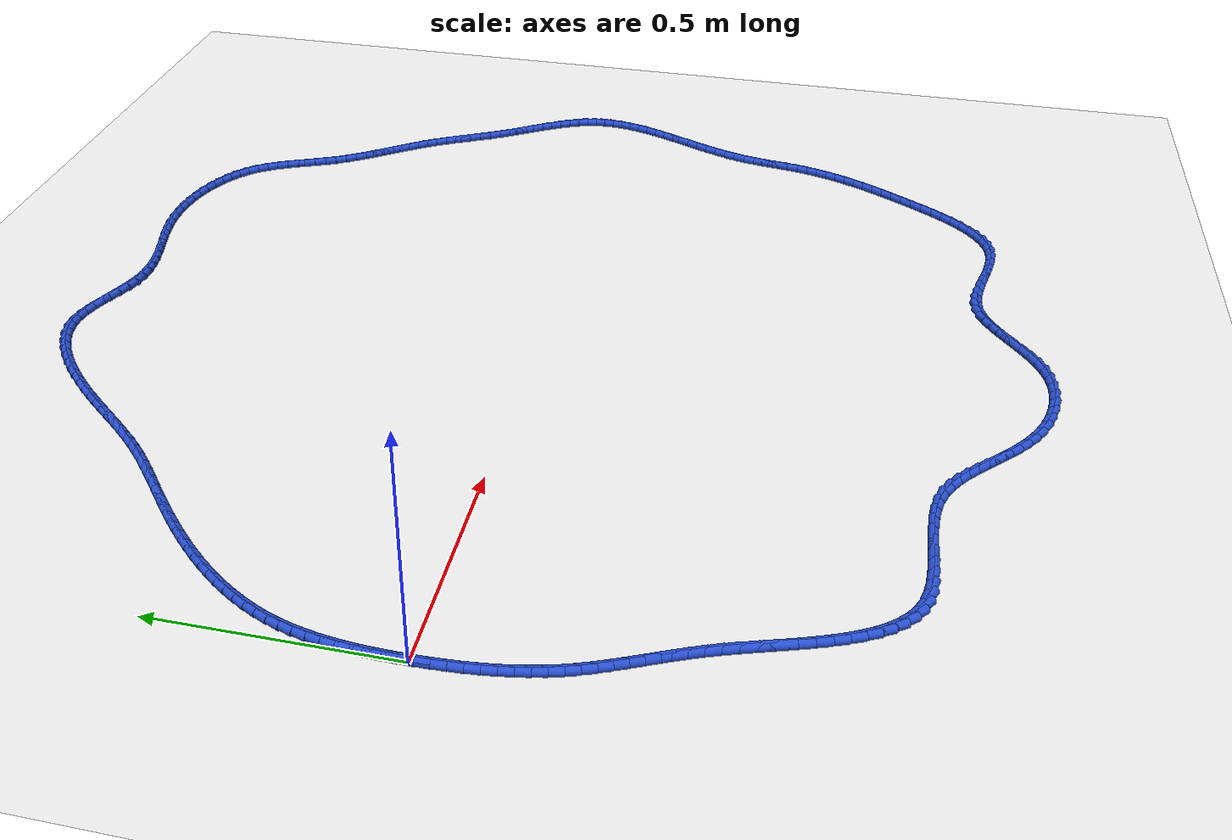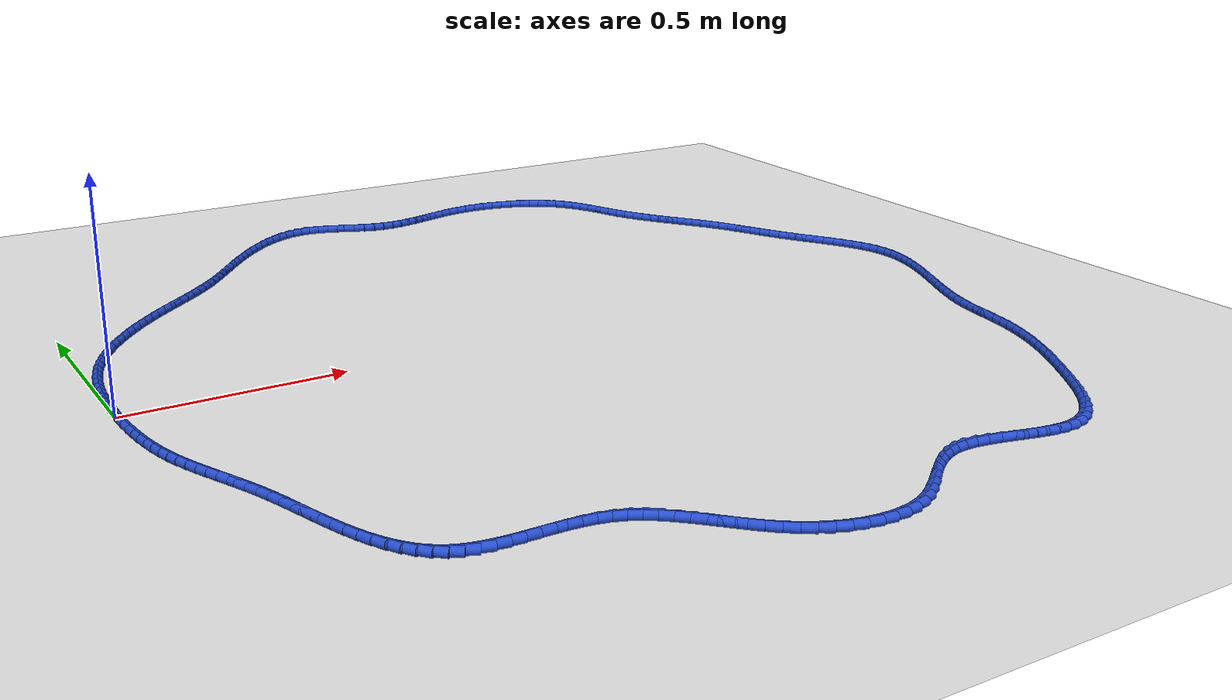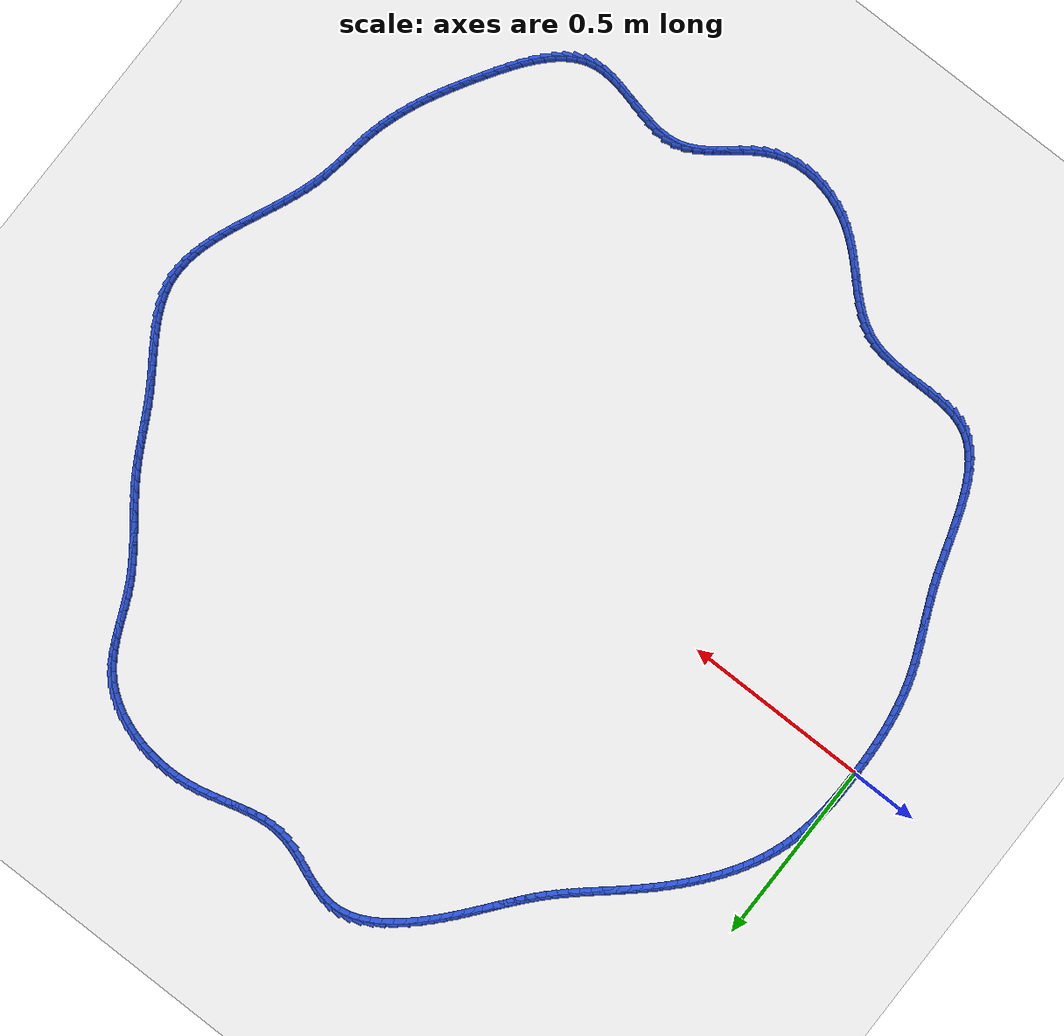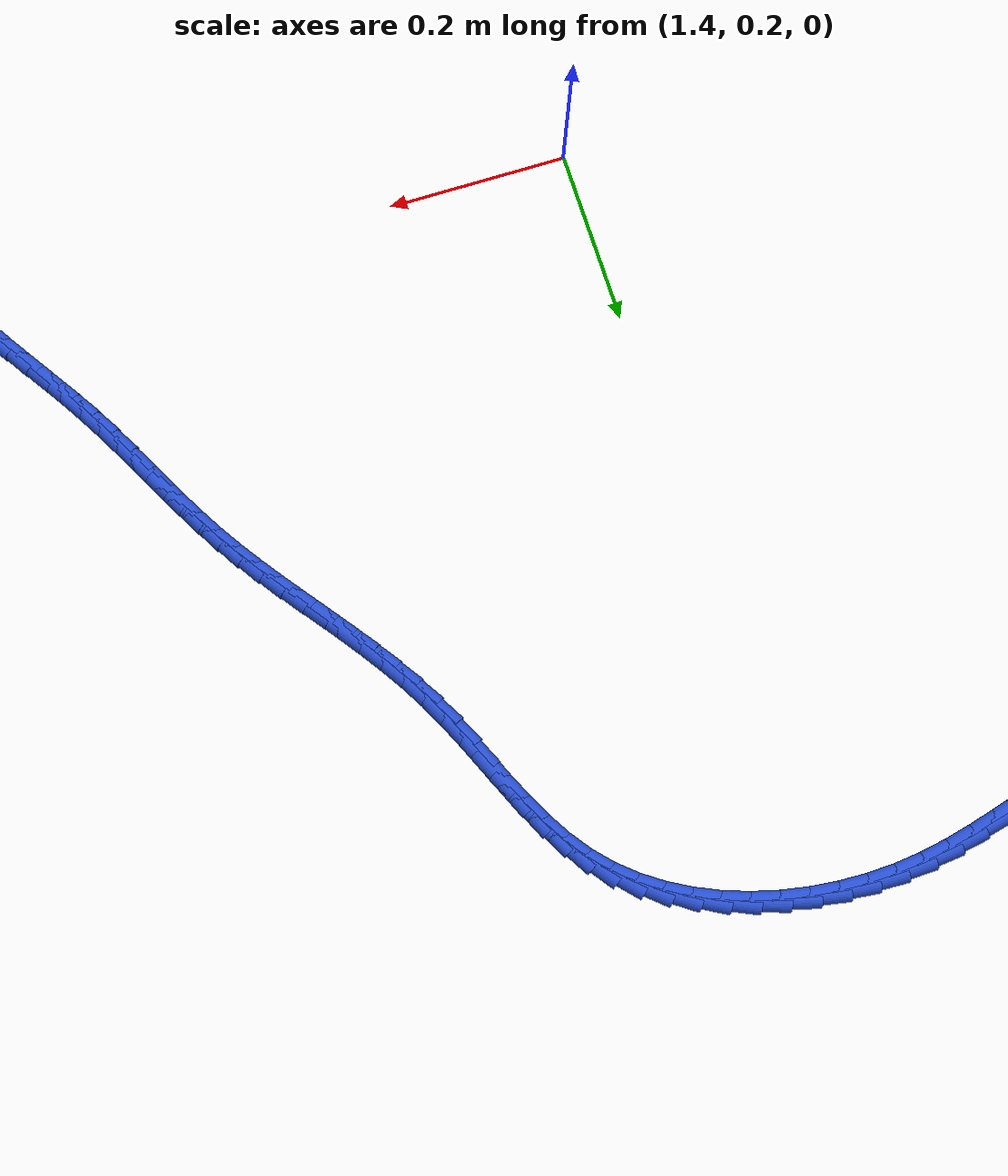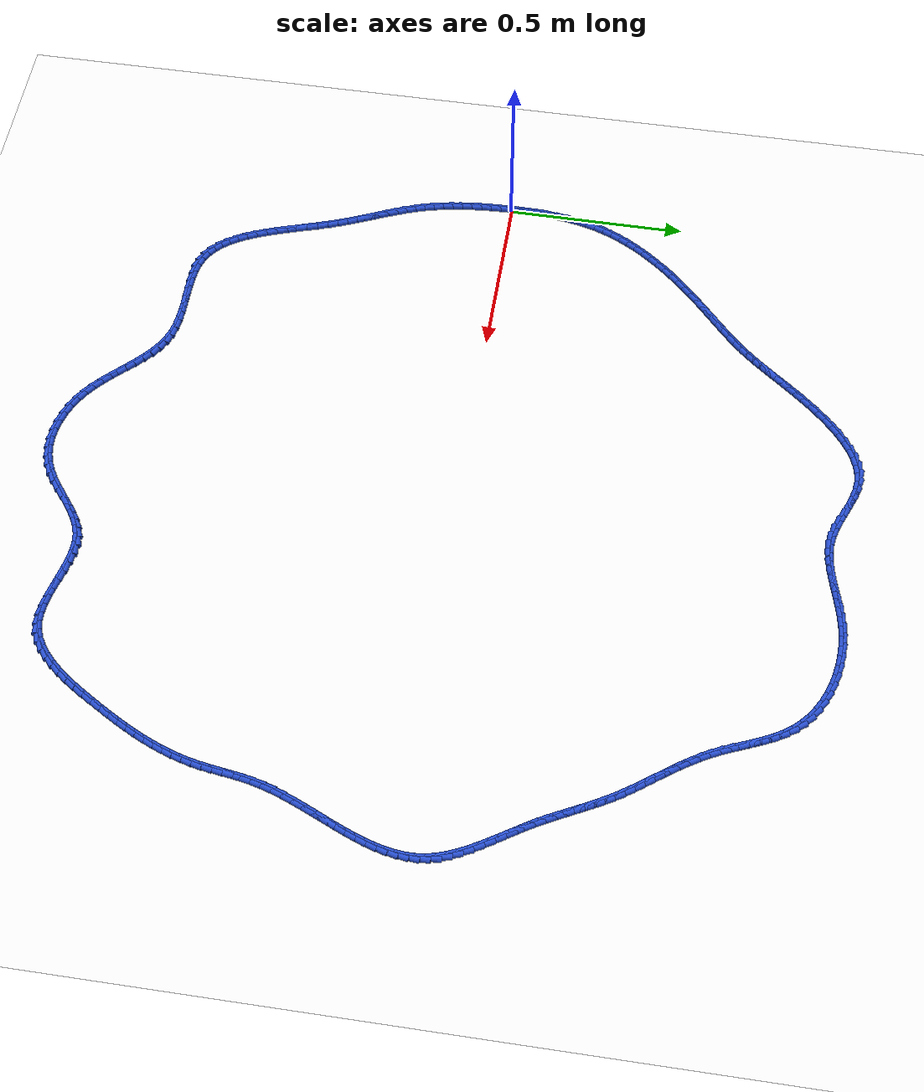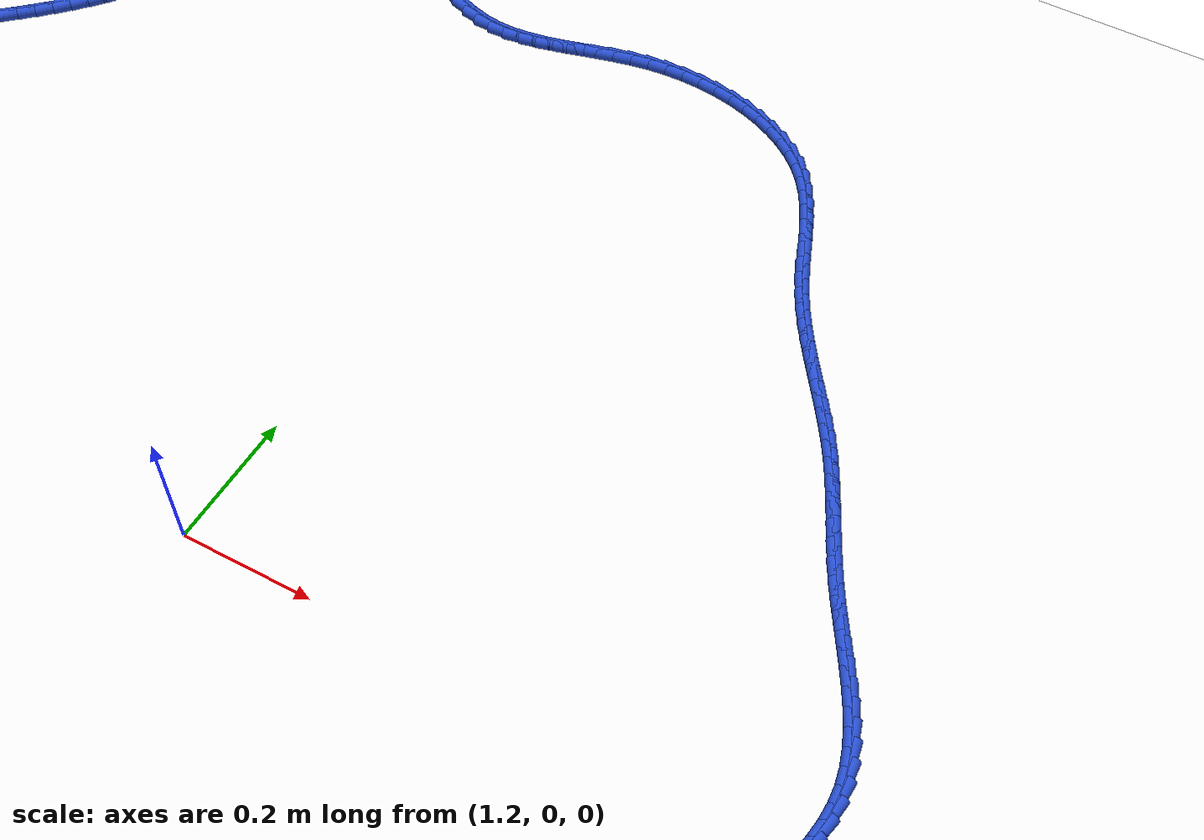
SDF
<sdf version="1.6">
 <world name="default">
  <light name="sun" type="directional">
   <pose>0 0 10 0 -0 0</pose>
   <diffuse>0.8 0.8 0.8 1</diffuse>
   <specular>0.2 0.2 0.2 1</specular>
   <attenuation>
    <range>1000</range>
    <constant>0.9</constant>
    <linear>0.01</linear>
    <quadratic>0.001</quadratic>
   </attenuation>
   <direction>-0.5 0.1 -0.9</direction>
  </light>
  <model name="ground_plane">
   <static>1</static>
   <link name="link">
    <collision name="collision">
     <geometry><plane><normal>0 0 1</normal><size>100 100</size></plane></geometry>
     <surface><friction><ode><mu>100</mu><mu2>50</mu2></ode></friction></surface>
    </collision>
    <visual name="visual">
     <cast_shadows>0</cast_shadows>
     <geometry><plane><normal>0 0 1</normal><size>100 100</size></plane></geometry>
     <material>
      <script><uri>file://media/materials/scripts/gazebo.material</uri><name>Gazebo/WhiteGlow</name></script>
     </material>
    </visual>
   </link>
  </model>
  <gravity>0 0 -9.8</gravity>
  <magnetic_field>6e-06 2.3e-05 -4.2e-05</magnetic_field>
  <atmosphere type="adiabatic"/>
  <physics name="default_physics" default="0" type="ode">
   <max_step_size>0.001</max_step_size>
   <real_time_factor>1</real_time_factor>
   <real_time_update_rate>1000</real_time_update_rate>
  </physics>
  <scene><ambient>0.4 0.4 0.4 1</ambient><background>0.7 0.7 0.7 1</background><shadows>1</shadows></scene>
  <spherical_coordinates>
   <surface_model>EARTH_WGS84</surface_model>
   <latitude_deg>0</latitude_deg>
   <longitude_deg>0</longitude_deg>
   <elevation>0</elevation>
   <heading_deg>0</heading_deg>
  </spherical_coordinates>
  <model name="line">
   <link name="link_0">
    <pose>-3.469446951953614e-18 -4.85722573273506e-17 0.01 0 1.57 1.5706727892045793</pose>
    <collision name="collision">
     <geometry><cylinder><radius>0.01</radius><length>0.08</length></cylinder></geometry>
    </collision>
    <visual name="visual">
     <material>
      <script><name>Gazebo/Blue</name><uri>file://media/materials/scripts/gazebo.material</uri></script>
     </material>
     <geometry><cylinder><radius>0.01</radius><length>0.08</length></cylinder></geometry>
    </visual>
   </link>
   <link name="link_1">
    <pose>3.5528886475424563e-06 0.0287595752867521 0.01 0 1.57 1.5489522809408764</pose>
    <collision name="collision">
     <geometry><cylinder><radius>0.01</radius><length>0.08</length></cylinder></geometry>
    </collision>
    <visual name="visual">
     <material>
      <script><name>Gazebo/Blue</name><uri>file://media/materials/scripts/gazebo.material</uri></script>
     </material>
     <geometry><cylinder><radius>0.01</radius><length>0.08</length></cylinder></geometry>
    </visual>
   </link>
   <link name="link_2">
    <pose>0.0006304451668905879 0.057453553017089924 0.01 0 1.57 1.5232653918438757</pose>
    <collision name="collision">
     <geometry><cylinder><radius>0.01</radius><length>0.08</length></cylinder></geometry>
    </collision>
    <visual name="visual">
     <material>
      <script><name>Gazebo/Blue</name><uri>file://media/materials/scripts/gazebo.material</uri></script>
     </material>
     <geometry><cylinder><radius>0.01</radius><length>0.08</length></cylinder></geometry>
    </visual>
   </link>
   <link name="link_3">
    <pose>0.001989441794584432 0.08602385285427798 0.01 0 1.57 1.4934595465308282</pose>
    <collision name="collision">
     <geometry><cylinder><radius>0.01</radius><length>0.08</length></cylinder></geometry>
    </collision>
    <visual name="visual">
     <material>
      <script><name>Gazebo/Blue</name><uri>file://media/materials/scripts/gazebo.material</uri></script>
     </material>
     <geometry><cylinder><radius>0.01</radius><length>0.08</length></cylinder></geometry>
    </visual>
   </link>
   <link name="link_4">
    <pose>0.004189307731584379 0.11441239446158094 0.01 0 1.57 1.4593718225182803</pose>
    <collision name="collision">
     <geometry><cylinder><radius>0.01</radius><length>0.08</length></cylinder></geometry>
    </collision>
    <visual name="visual">
     <material>
      <script><name>Gazebo/Blue</name><uri>file://media/materials/scripts/gazebo.material</uri></script>
     </material>
     <geometry><cylinder><radius>0.01</radius><length>0.08</length></cylinder></geometry>
    </visual>
   </link>
   <link name="link_5">
    <pose>0.007338807937745731 0.14256109750226337 0.01 0 1.57 1.4208431871317464</pose>
    <collision name="collision">
     <geometry><cylinder><radius>0.01</radius><length>0.08</length></cylinder></geometry>
    </collision>
    <visual name="visual">
     <material>
      <script><name>Gazebo/Blue</name><uri>file://media/materials/scripts/gazebo.material</uri></script>
     </material>
     <geometry><cylinder><radius>0.01</radius><length>0.08</length></cylinder></geometry>
    </visual>
   </link>
   <link name="link_6">
    <pose>0.011546707372923794 0.17041188163958992 0.01 0 1.57 1.3777372547432474</pose>
    <collision name="collision">
     <geometry><cylinder><radius>0.01</radius><length>0.08</length></cylinder></geometry>
    </collision>
    <visual name="visual">
     <material>
      <script><name>Gazebo/Blue</name><uri>file://media/materials/scripts/gazebo.material</uri></script>
     </material>
     <geometry><cylinder><radius>0.01</radius><length>0.08</length></cylinder></geometry>
    </visual>
   </link>
   <link name="link_7">
    <pose>0.01692177099697386 0.1979066665368252 0.01 0 1.57 1.3299640991069586</pose>
    <collision name="collision">
     <geometry><cylinder><radius>0.01</radius><length>0.08</length></cylinder></geometry>
    </collision>
    <visual name="visual">
     <material>
      <script><name>Gazebo/Blue</name><uri>file://media/materials/scripts/gazebo.material</uri></script>
     </material>
     <geometry><cylinder><radius>0.01</radius><length>0.08</length></cylinder></geometry>
    </visual>
   </link>
   <link name="link_8">
    <pose>0.023572763769751245 0.22498737185723383 0.01 0 1.57 1.2775089130807966</pose>
    <collision name="collision">
     <geometry><cylinder><radius>0.01</radius><length>0.08</length></cylinder></geometry>
    </collision>
    <visual name="visual">
     <material>
      <script><name>Gazebo/Blue</name><uri>file://media/materials/scripts/gazebo.material</uri></script>
     </material>
     <geometry><cylinder><radius>0.01</radius><length>0.08</length></cylinder></geometry>
    </visual>
   </link>
   <link name="link_9">
    <pose>0.031608450651111245 0.2515959172640805 0.01 0 1.57 1.2209503418457286</pose>
    <collision name="collision">
     <geometry><cylinder><radius>0.01</radius><length>0.08</length></cylinder></geometry>
    </collision>
    <visual name="visual">
     <material>
      <script><name>Gazebo/Blue</name><uri>file://media/materials/scripts/gazebo.material</uri></script>
     </material>
     <geometry><cylinder><radius>0.01</radius><length>0.08</length></cylinder></geometry>
    </visual>
   </link>
   <link name="link_10">
    <pose>0.041124724547704376 0.27767833581572926 0.01 0 1.57 1.165088919046137</pose>
    <collision name="collision">
     <geometry><cylinder><radius>0.01</radius><length>0.08</length></cylinder></geometry>
    </collision>
    <visual name="visual">
     <material>
      <script><name>Gazebo/Blue</name><uri>file://media/materials/scripts/gazebo.material</uri></script>
     </material>
     <geometry><cylinder><radius>0.01</radius><length>0.08</length></cylinder></geometry>
    </visual>
   </link>
   <link name="link_11">
    <pose>0.052095644841664776 0.3032195937084639 0.01 0 1.57 1.1126270308486028</pose>
    <collision name="collision">
     <geometry><cylinder><radius>0.01</radius><length>0.08</length></cylinder></geometry>
    </collision>
    <visual name="visual">
     <material>
      <script><name>Gazebo/Blue</name><uri>file://media/materials/scripts/gazebo.material</uri></script>
     </material>
     <geometry><cylinder><radius>0.01</radius><length>0.08</length></cylinder></geometry>
    </visual>
   </link>
   <link name="link_12">
    <pose>0.06442812869197069 0.32822611311667155 0.01 0 1.57 1.0636623158189433</pose>
    <collision name="collision">
     <geometry><cylinder><radius>0.01</radius><length>0.08</length></cylinder></geometry>
    </collision>
    <visual name="visual">
     <material>
      <script><name>Gazebo/Blue</name><uri>file://media/materials/scripts/gazebo.material</uri></script>
     </material>
     <geometry><cylinder><radius>0.01</radius><length>0.08</length></cylinder></geometry>
    </visual>
   </link>
   <link name="link_13">
    <pose>0.07802839228216304 0.3527045402185469 0.01 0 1.57 1.0181881492837634</pose>
    <collision name="collision">
     <geometry><cylinder><radius>0.01</radius><length>0.08</length></cylinder></geometry>
    </collision>
    <visual name="visual">
     <material>
      <script><name>Gazebo/Blue</name><uri>file://media/materials/scripts/gazebo.material</uri></script>
     </material>
     <geometry><cylinder><radius>0.01</radius><length>0.08</length></cylinder></geometry>
    </visual>
   </link>
   <link name="link_14">
    <pose>0.09280265179578287 0.3766615211922848 0.01 0 1.57 0.976138756294928</pose>
    <collision name="collision">
     <geometry><cylinder><radius>0.01</radius><length>0.08</length></cylinder></geometry>
    </collision>
    <visual name="visual">
     <material>
      <script><name>Gazebo/Blue</name><uri>file://media/materials/scripts/gazebo.material</uri></script>
     </material>
     <geometry><cylinder><radius>0.01</radius><length>0.08</length></cylinder></geometry>
    </visual>
   </link>
   <link name="link_15">
    <pose>0.10865712341637107 0.40010370221607977 0.01 0 1.57 0.9374065995087001</pose>
    <collision name="collision">
     <geometry><cylinder><radius>0.01</radius><length>0.08</length></cylinder></geometry>
    </collision>
    <visual name="visual">
     <material>
      <script><name>Gazebo/Blue</name><uri>file://media/materials/scripts/gazebo.material</uri></script>
     </material>
     <geometry><cylinder><radius>0.01</radius><length>0.08</length></cylinder></geometry>
    </visual>
   </link>
   <link name="link_16">
    <pose>0.12549802332746873 0.4230377294681269 0.01 0 1.57 0.901857479022272</pose>
    <collision name="collision">
     <geometry><cylinder><radius>0.01</radius><length>0.08</length></cylinder></geometry>
    </collision>
    <visual name="visual">
     <material>
      <script><name>Gazebo/Blue</name><uri>file://media/materials/scripts/gazebo.material</uri></script>
     </material>
     <geometry><cylinder><radius>0.01</radius><length>0.08</length></cylinder></geometry>
    </visual>
   </link>
   <link name="link_17">
    <pose>0.14323156771261675 0.4454702491266208 0.01 0 1.57 0.8693429496021429</pose>
    <collision name="collision">
     <geometry><cylinder><radius>0.01</radius><length>0.08</length></cylinder></geometry>
    </collision>
    <visual name="visual">
     <material>
      <script><name>Gazebo/Blue</name><uri>file://media/materials/scripts/gazebo.material</uri></script>
     </material>
     <geometry><cylinder><radius>0.01</radius><length>0.08</length></cylinder></geometry>
    </visual>
   </link>
   <link name="link_18">
    <pose>0.16176397275535612 0.4674079073697562 0.01 0 1.57 0.8397101017526116</pose>
    <collision name="collision">
     <geometry><cylinder><radius>0.01</radius><length>0.08</length></cylinder></geometry>
    </collision>
    <visual name="visual">
     <material>
      <script><name>Gazebo/Blue</name><uri>file://media/materials/scripts/gazebo.material</uri></script>
     </material>
     <geometry><cylinder><radius>0.01</radius><length>0.08</length></cylinder></geometry>
    </visual>
   </link>
   <link name="link_19">
    <pose>0.18100145463922784 0.4888573503757278 0.01 0 1.57 0.8128090061743278</pose>
    <collision name="collision">
     <geometry><cylinder><radius>0.01</radius><length>0.08</length></cylinder></geometry>
    </collision>
    <visual name="visual">
     <material>
      <script><name>Gazebo/Blue</name><uri>file://media/materials/scripts/gazebo.material</uri></script>
     </material>
     <geometry><cylinder><radius>0.01</radius><length>0.08</length></cylinder></geometry>
    </visual>
   </link>
   <link name="link_20">
    <pose>0.20085022954777282 0.5098252243227305 0.01 0 1.57 0.7884982347308077</pose>
    <collision name="collision">
     <geometry><cylinder><radius>0.01</radius><length>0.08</length></cylinder></geometry>
    </collision>
    <visual name="visual">
     <material>
      <script><name>Gazebo/Blue</name><uri>file://media/materials/scripts/gazebo.material</uri></script>
     </material>
     <geometry><cylinder><radius>0.01</radius><length>0.08</length></cylinder></geometry>
    </visual>
   </link>
   <link name="link_21">
    <pose>0.22121651366453216 0.530318175388959 0.01 0 1.57 0.7666488950104318</pose>
    <collision name="collision">
     <geometry><cylinder><radius>0.01</radius><length>0.08</length></cylinder></geometry>
    </collision>
    <visual name="visual">
     <material>
      <script><name>Gazebo/Blue</name><uri>file://media/materials/scripts/gazebo.material</uri></script>
     </material>
     <geometry><cylinder><radius>0.01</radius><length>0.08</length></cylinder></geometry>
    </visual>
   </link>
   <link name="link_22">
    <pose>0.24200652317304677 0.550342849752608 0.01 0 1.57 0.7471494016440369</pose>
    <collision name="collision">
     <geometry><cylinder><radius>0.01</radius><length>0.08</length></cylinder></geometry>
    </collision>
    <visual name="visual">
     <material>
      <script><name>Gazebo/Blue</name><uri>file://media/materials/scripts/gazebo.material</uri></script>
     </material>
     <geometry><cylinder><radius>0.01</radius><length>0.08</length></cylinder></geometry>
    </visual>
   </link>
   <link name="link_23">
    <pose>0.2631264561891999 0.569905947927536 0.01 0 1.57 0.7309272539567916</pose>
    <collision name="collision">
     <geometry><cylinder><radius>0.01</radius><length>0.08</length></cylinder></geometry>
    </collision>
    <visual name="visual">
     <material>
      <script><name>Gazebo/Blue</name><uri>file://media/materials/scripts/gazebo.material</uri></script>
     </material>
     <geometry><cylinder><radius>0.01</radius><length>0.08</length></cylinder></geometry>
    </visual>
   </link>
   <link name="link_24">
    <pose>0.28447242442853177 0.5890445037037293 0.01 0 1.57 0.7206941612121894</pose>
    <collision name="collision">
     <geometry><cylinder><radius>0.01</radius><length>0.08</length></cylinder></geometry>
    </collision>
    <visual name="visual">
     <material>
      <script><name>Gazebo/Blue</name><uri>file://media/materials/scripts/gazebo.material</uri></script>
     </material>
     <geometry><cylinder><radius>0.01</radius><length>0.08</length></cylinder></geometry>
    </visual>
   </link>
   <link name="link_25">
    <pose>0.30591368959123283 0.6078762981052732 0.01 0 1.57 0.7169711343749038</pose>
    <collision name="collision">
     <geometry><cylinder><radius>0.01</radius><length>0.08</length></cylinder></geometry>
    </collision>
    <visual name="visual">
     <material>
      <script><name>Gazebo/Blue</name><uri>file://media/materials/scripts/gazebo.material</uri></script>
     </material>
     <geometry><cylinder><radius>0.01</radius><length>0.08</length></cylinder></geometry>
    </visual>
   </link>
   <link name="link_26">
    <pose>0.3273150946372849 0.6265324008283589 0.01 0 1.57 0.7198534562208936</pose>
    <collision name="collision">
     <geometry><cylinder><radius>0.01</radius><length>0.08</length></cylinder></geometry>
    </collision>
    <visual name="visual">
     <material>
      <script><name>Gazebo/Blue</name><uri>file://media/materials/scripts/gazebo.material</uri></script>
     </material>
     <geometry><cylinder><radius>0.01</radius><length>0.08</length></cylinder></geometry>
    </visual>
   </link>
   <link name="link_27">
    <pose>0.3485414825266697 0.6451438815691772 0.01 0 1.57 0.7294592777876213</pose>
    <collision name="collision">
     <geometry><cylinder><radius>0.01</radius><length>0.08</length></cylinder></geometry>
    </collision>
    <visual name="visual">
     <material>
      <script><name>Gazebo/Blue</name><uri>file://media/materials/scripts/gazebo.material</uri></script>
     </material>
     <geometry><cylinder><radius>0.01</radius><length>0.08</length></cylinder></geometry>
    </visual>
   </link>
   <link name="link_28">
    <pose>0.3694576962193693 0.6638418100239193 0.01 0 1.57 0.7459268850918639</pose>
    <collision name="collision">
     <geometry><cylinder><radius>0.01</radius><length>0.08</length></cylinder></geometry>
    </collision>
    <visual name="visual">
     <material>
      <script><name>Gazebo/Blue</name><uri>file://media/materials/scripts/gazebo.material</uri></script>
     </material>
     <geometry><cylinder><radius>0.01</radius><length>0.08</length></cylinder></geometry>
    </visual>
   </link>
   <link name="link_29">
    <pose>0.38992857867536546 0.6827572558887759 0.01 0 1.57 0.7694023276488269</pose>
    <collision name="collision">
     <geometry><cylinder><radius>0.01</radius><length>0.08</length></cylinder></geometry>
    </collision>
    <visual name="visual">
     <material>
      <script><name>Gazebo/Blue</name><uri>file://media/materials/scripts/gazebo.material</uri></script>
     </material>
     <geometry><cylinder><radius>0.01</radius><length>0.08</length></cylinder></geometry>
    </visual>
   </link>
   <link name="link_30">
    <pose>0.40981897285464003 0.7020212888599382 0.01 0 1.57 0.7999702303431748</pose>
    <collision name="collision">
     <geometry><cylinder><radius>0.01</radius><length>0.08</length></cylinder></geometry>
    </collision>
    <visual name="visual">
     <material>
      <script><name>Gazebo/Blue</name><uri>file://media/materials/scripts/gazebo.material</uri></script>
     </material>
     <geometry><cylinder><radius>0.01</radius><length>0.08</length></cylinder></geometry>
    </visual>
   </link>
   <link name="link_31">
    <pose>0.4289948070415806 0.7217642910821758 0.01 0 1.57 0.8331201504467286</pose>
    <collision name="collision">
     <geometry><cylinder><radius>0.01</radius><length>0.08</length></cylinder></geometry>
    </collision>
    <visual name="visual">
     <material>
      <script><name>Gazebo/Blue</name><uri>file://media/materials/scripts/gazebo.material</uri></script>
     </material>
     <geometry><cylinder><radius>0.01</radius><length>0.08</length></cylinder></geometry>
    </visual>
   </link>
   <link name="link_32">
    <pose>0.44742975217353964 0.7420483898874648 0.01 0 1.57 0.8602502442624418</pose>
    <collision name="collision">
     <geometry><cylinder><radius>0.01</radius><length>0.08</length></cylinder></geometry>
    </collision>
    <visual name="visual">
     <material>
      <script><name>Gazebo/Blue</name><uri>file://media/materials/scripts/gazebo.material</uri></script>
     </material>
     <geometry><cylinder><radius>0.01</radius><length>0.08</length></cylinder></geometry>
    </visual>
   </link>
   <link name="link_33">
    <pose>0.46529511399538026 0.7628105112467868 0.01 0 1.57 0.880203145737088</pose>
    <collision name="collision">
     <geometry><cylinder><radius>0.01</radius><length>0.08</length></cylinder></geometry>
    </collision>
    <visual name="visual">
     <material>
      <script><name>Gazebo/Blue</name><uri>file://media/materials/scripts/gazebo.material</uri></script>
     </material>
     <geometry><cylinder><radius>0.01</radius><length>0.08</length></cylinder></geometry>
    </visual>
   </link>
   <link name="link_34">
    <pose>0.4827833637068355 0.7839741728464735 0.01 0 1.57 0.8928675080751223</pose>
    <collision name="collision">
     <geometry><cylinder><radius>0.01</radius><length>0.08</length></cylinder></geometry>
    </collision>
    <visual name="visual">
     <material>
      <script><name>Gazebo/Blue</name><uri>file://media/materials/scripts/gazebo.material</uri></script>
     </material>
     <geometry><cylinder><radius>0.01</radius><length>0.08</length></cylinder></geometry>
    </visual>
   </link>
   <link name="link_35">
    <pose>0.5000869725076386 0.8054628923728573 0.01 0 1.57 0.8982583832611836</pose>
    <collision name="collision">
     <geometry><cylinder><radius>0.01</radius><length>0.08</length></cylinder></geometry>
    </collision>
    <visual name="visual">
     <material>
      <script><name>Gazebo/Blue</name><uri>file://media/materials/scripts/gazebo.material</uri></script>
     </material>
     <geometry><cylinder><radius>0.01</radius><length>0.08</length></cylinder></geometry>
    </visual>
   </link>
   <link name="link_36">
    <pose>0.5173984115975223 0.8272001875122692 0.01 0 1.57 0.8964944354219363</pose>
    <collision name="collision">
     <geometry><cylinder><radius>0.01</radius><length>0.08</length></cylinder></geometry>
    </collision>
    <visual name="visual">
     <material>
      <script><name>Gazebo/Blue</name><uri>file://media/materials/scripts/gazebo.material</uri></script>
     </material>
     <geometry><cylinder><radius>0.01</radius><length>0.08</length></cylinder></geometry>
    </visual>
   </link>
   <link name="link_37">
    <pose>0.5349101521762201 0.849109575951042 0.01 0 1.57 0.8877834778519994</pose>
    <collision name="collision">
     <geometry><cylinder><radius>0.01</radius><length>0.08</length></cylinder></geometry>
    </collision>
    <visual name="visual">
     <material>
      <script><name>Gazebo/Blue</name><uri>file://media/materials/scripts/gazebo.material</uri></script>
     </material>
     <geometry><cylinder><radius>0.01</radius><length>0.08</length></cylinder></geometry>
    </visual>
   </link>
   <link name="link_38">
    <pose>0.5528146654434647 0.8711145753755072 0.01 0 1.57 0.8724163662346153</pose>
    <collision name="collision">
     <geometry><cylinder><radius>0.01</radius><length>0.08</length></cylinder></geometry>
    </collision>
    <visual name="visual">
     <material>
      <script><name>Gazebo/Blue</name><uri>file://media/materials/scripts/gazebo.material</uri></script>
     </material>
     <geometry><cylinder><radius>0.01</radius><length>0.08</length></cylinder></geometry>
    </visual>
   </link>
   <link name="link_39">
    <pose>0.5713044225989897 0.893138703471997 0.01 0 1.57 0.8507675223047537</pose>
    <collision name="collision">
     <geometry><cylinder><radius>0.01</radius><length>0.08</length></cylinder></geometry>
    </collision>
    <visual name="visual">
     <material>
      <script><name>Gazebo/Blue</name><uri>file://media/materials/scripts/gazebo.material</uri></script>
     </material>
     <geometry><cylinder><radius>0.01</radius><length>0.08</length></cylinder></geometry>
    </visual>
   </link>
   <link name="link_40">
    <pose>0.5905718948425275 0.915105477926843 0.01 0 1.57 0.8232991175520333</pose>
    <collision name="collision">
     <geometry><cylinder><radius>0.01</radius><length>0.08</length></cylinder></geometry>
    </collision>
    <visual name="visual">
     <material>
      <script><name>Gazebo/Blue</name><uri>file://media/materials/scripts/gazebo.material</uri></script>
     </material>
     <geometry><cylinder><radius>0.01</radius><length>0.08</length></cylinder></geometry>
    </visual>
   </link>
   <link name="link_41">
    <pose>0.6108095526507975 0.9369384153739746 0.01 0 1.57 0.7900038570666732</pose>
    <collision name="collision">
     <geometry><cylinder><radius>0.01</radius><length>0.08</length></cylinder></geometry>
    </collision>
    <visual name="visual">
     <material>
      <script><name>Gazebo/Blue</name><uri>file://media/materials/scripts/gazebo.material</uri></script>
     </material>
     <geometry><cylinder><radius>0.01</radius><length>0.08</length></cylinder></geometry>
    </visual>
   </link>
   <link name="link_42">
    <pose>0.6321555042083911 0.9584819039512215 0.01 0 1.57 0.7486959255549774</pose>
    <collision name="collision">
     <geometry><cylinder><radius>0.01</radius><length>0.08</length></cylinder></geometry>
    </collision>
    <visual name="visual">
     <material>
      <script><name>Gazebo/Blue</name><uri>file://media/materials/scripts/gazebo.material</uri></script>
     </material>
     <geometry><cylinder><radius>0.01</radius><length>0.08</length></cylinder></geometry>
    </visual>
   </link>
   <link name="link_43">
    <pose>0.6545456667338362 0.9792860272988753 0.01 0 1.57 0.6975241856056223</pose>
    <collision name="collision">
     <geometry><cylinder><radius>0.01</radius><length>0.08</length></cylinder></geometry>
    </collision>
    <visual name="visual">
     <material>
      <script><name>Gazebo/Blue</name><uri>file://media/materials/scripts/gazebo.material</uri></script>
     </material>
     <geometry><cylinder><radius>0.01</radius><length>0.08</length></cylinder></geometry>
    </visual>
   </link>
   <link name="link_44">
    <pose>0.6778689600877729 0.9988324607892015 0.01 0 1.57 0.6344658465230945</pose>
    <collision name="collision">
     <geometry><cylinder><radius>0.01</radius><length>0.08</length></cylinder></geometry>
    </collision>
    <visual name="visual">
     <material>
      <script><name>Gazebo/Blue</name><uri>file://media/materials/scripts/gazebo.material</uri></script>
     </material>
     <geometry><cylinder><radius>0.01</radius><length>0.08</length></cylinder></geometry>
    </visual>
   </link>
   <link name="link_45">
    <pose>0.7020143041308403 1.0166028797944655 0.01 0 1.57 0.5568872210970363</pose>
    <collision name="collision">
     <geometry><cylinder><radius>0.01</radius><length>0.08</length></cylinder></geometry>
    </collision>
    <visual name="visual">
     <material>
      <script><name>Gazebo/Blue</name><uri>file://media/materials/scripts/gazebo.material</uri></script>
     </material>
     <geometry><cylinder><radius>0.01</radius><length>0.08</length></cylinder></geometry>
    </visual>
   </link>
   <link name="link_46">
    <pose>0.7268706187236783 1.0320789596869335 0.01 0 1.57 0.4616126764074338</pose>
    <collision name="collision">
     <geometry><cylinder><radius>0.01</radius><length>0.08</length></cylinder></geometry>
    </collision>
    <visual name="visual">
     <material>
      <script><name>Gazebo/Blue</name><uri>file://media/materials/scripts/gazebo.material</uri></script>
     </material>
     <geometry><cylinder><radius>0.01</radius><length>0.08</length></cylinder></geometry>
    </visual>
   </link>
   <link name="link_47">
    <pose>0.7523268237269267 1.0447423758388699 0.01 0 1.57 0.34529017203838597</pose>
    <collision name="collision">
     <geometry><cylinder><radius>0.01</radius><length>0.08</length></cylinder></geometry>
    </collision>
    <visual name="visual">
     <material>
      <script><name>Gazebo/Blue</name><uri>file://media/materials/scripts/gazebo.material</uri></script>
     </material>
     <geometry><cylinder><radius>0.01</radius><length>0.08</length></cylinder></geometry>
    </visual>
   </link>
   <link name="link_48">
    <pose>0.778271839001225 1.0540748036225411 0.01 0 1.57 0.20536660697648249</pose>
    <collision name="collision">
     <geometry><cylinder><radius>0.01</radius><length>0.08</length></cylinder></geometry>
    </collision>
    <visual name="visual">
     <material>
      <script><name>Gazebo/Blue</name><uri>file://media/materials/scripts/gazebo.material</uri></script>
     </material>
     <geometry><cylinder><radius>0.01</radius><length>0.08</length></cylinder></geometry>
    </visual>
   </link>
   <link name="link_49">
    <pose>0.8045945844072123 1.0595579184102117 0.01 0 1.57 0.04193933534597117</pose>
    <collision name="collision">
     <geometry><cylinder><radius>0.01</radius><length>0.08</length></cylinder></geometry>
    </collision>
    <visual name="visual">
     <material>
      <script><name>Gazebo/Blue</name><uri>file://media/materials/scripts/gazebo.material</uri></script>
     </material>
     <geometry><cylinder><radius>0.01</radius><length>0.08</length></cylinder></geometry>
    </visual>
   </link>
   <link name="link_50">
    <pose>0.8311839948935968 1.0606737148843681 0.01 0 1.57 -0.12609204755094047</pose>
    <collision name="collision">
     <geometry><cylinder><radius>0.01</radius><length>0.08</length></cylinder></geometry>
    </collision>
    <visual name="visual">
     <material>
      <script><name>Gazebo/Blue</name><uri>file://media/materials/scripts/gazebo.material</uri></script>
     </material>
     <geometry><cylinder><radius>0.01</radius><length>0.08</length></cylinder></geometry>
    </visual>
   </link>
   <link name="link_51">
    <pose>0.8579468170407604 1.0572811369919108 0.01 0 1.57 -0.2523971524667572</pose>
    <collision name="collision">
     <geometry><cylinder><radius>0.01</radius><length>0.08</length></cylinder></geometry>
    </collision>
    <visual name="visual">
     <material>
      <script><name>Gazebo/Blue</name><uri>file://media/materials/scripts/gazebo.material</uri></script>
     </material>
     <geometry><cylinder><radius>0.01</radius><length>0.08</length></cylinder></geometry>
    </visual>
   </link>
   <link name="link_52">
    <pose>0.8848420492527913 1.0503449390215331 0.01 0 1.57 -0.3322020160063515</pose>
    <collision name="collision">
     <geometry><cylinder><radius>0.01</radius><length>0.08</length></cylinder></geometry>
    </collision>
    <visual name="visual">
     <material>
      <script><name>Gazebo/Blue</name><uri>file://media/materials/scripts/gazebo.material</uri></script>
     </material>
     <geometry><cylinder><radius>0.01</radius><length>0.08</length></cylinder></geometry>
    </visual>
   </link>
   <link name="link_53">
    <pose>0.9118382222133586 1.0410316078062456 0.01 0 1.57 -0.37084151884248046</pose>
    <collision name="collision">
     <geometry><cylinder><radius>0.01</radius><length>0.08</length></cylinder></geometry>
    </collision>
    <visual name="visual">
     <material>
      <script><name>Gazebo/Blue</name><uri>file://media/materials/scripts/gazebo.material</uri></script>
     </material>
     <geometry><cylinder><radius>0.01</radius><length>0.08</length></cylinder></geometry>
    </visual>
   </link>
   <link name="link_54">
    <pose>0.938903866606132 1.0305076301790588 0.01 0 1.57 -0.37178289798972486</pose>
    <collision name="collision">
     <geometry><cylinder><radius>0.01</radius><length>0.08</length></cylinder></geometry>
    </collision>
    <visual name="visual">
     <material>
      <script><name>Gazebo/Blue</name><uri>file://media/materials/scripts/gazebo.material</uri></script>
     </material>
     <geometry><cylinder><radius>0.01</radius><length>0.08</length></cylinder></geometry>
    </visual>
   </link>
   <link name="link_55">
    <pose>0.96600751311478 1.019939492972983 0.01 0 1.57 -0.33526922763700157</pose>
    <collision name="collision">
     <geometry><cylinder><radius>0.01</radius><length>0.08</length></cylinder></geometry>
    </collision>
    <visual name="visual">
     <material>
      <script><name>Gazebo/Blue</name><uri>file://media/materials/scripts/gazebo.material</uri></script>
     </material>
     <geometry><cylinder><radius>0.01</radius><length>0.08</length></cylinder></geometry>
    </visual>
   </link>
   <link name="link_56">
    <pose>0.9931176924229725 1.0104936830210285 0.01 0 1.57 -0.2583351659881827</pose>
    <collision name="collision">
     <geometry><cylinder><radius>0.01</radius><length>0.08</length></cylinder></geometry>
    </collision>
    <visual name="visual">
     <material>
      <script><name>Gazebo/Blue</name><uri>file://media/materials/scripts/gazebo.material</uri></script>
     </material>
     <geometry><cylinder><radius>0.01</radius><length>0.08</length></cylinder></geometry>
    </visual>
   </link>
   <link name="link_57">
    <pose>1.0202029352143782 1.003336687156206 0.01 0 1.57 -0.13931413505435927</pose>
    <collision name="collision">
     <geometry><cylinder><radius>0.01</radius><length>0.08</length></cylinder></geometry>
    </collision>
    <visual name="visual">
     <material>
      <script><name>Gazebo/Blue</name><uri>file://media/materials/scripts/gazebo.material</uri></script>
     </material>
     <geometry><cylinder><radius>0.01</radius><length>0.08</length></cylinder></geometry>
    </visual>
   </link>
   <link name="link_58">
    <pose>1.0472367196017982 0.9995459429476409 0.01 0 1.57 -0.0137700161365197</pose>
    <collision name="collision">
     <geometry><cylinder><radius>0.01</radius><length>0.08</length></cylinder></geometry>
    </collision>
    <visual name="visual">
     <material>
      <script><name>Gazebo/Blue</name><uri>file://media/materials/scripts/gazebo.material</uri></script>
     </material>
     <geometry><cylinder><radius>0.01</radius><length>0.08</length></cylinder></geometry>
    </visual>
   </link>
   <link name="link_59">
    <pose>1.0742494673558012 0.9991739534634893 0.01 0 1.57 0.09003630734448476</pose>
    <collision name="collision">
     <geometry><cylinder><radius>0.01</radius><length>0.08</length></cylinder></geometry>
    </collision>
    <visual name="visual">
     <material>
      <script><name>Gazebo/Blue</name><uri>file://media/materials/scripts/gazebo.material</uri></script>
     </material>
     <geometry><cylinder><radius>0.01</radius><length>0.08</length></cylinder></geometry>
    </visual>
   </link>
   <link name="link_60">
    <pose>1.1013080691349342 1.0016168146677393 0.01 0 1.57 0.16924322976613373</pose>
    <collision name="collision">
     <geometry><cylinder><radius>0.01</radius><length>0.08</length></cylinder></geometry>
    </collision>
    <visual name="visual">
     <material>
      <script><name>Gazebo/Blue</name><uri>file://media/materials/scripts/gazebo.material</uri></script>
     </material>
     <geometry><cylinder><radius>0.01</radius><length>0.08</length></cylinder></geometry>
    </visual>
   </link>
   <link name="link_61">
    <pose>1.128480011442463 1.006259897856595 0.01 0 1.57 0.22389852214442468</pose>
    <collision name="collision">
     <geometry><cylinder><radius>0.01</radius><length>0.08</length></cylinder></geometry>
    </collision>
    <visual name="visual">
     <material>
      <script><name>Gazebo/Blue</name><uri>file://media/materials/scripts/gazebo.material</uri></script>
     </material>
     <geometry><cylinder><radius>0.01</radius><length>0.08</length></cylinder></geometry>
    </visual>
   </link>
   <link name="link_62">
    <pose>1.1558327807816549 1.0124885743262615 0.01 0 1.57 0.2551606315116729</pose>
    <collision name="collision">
     <geometry><cylinder><radius>0.01</radius><length>0.08</length></cylinder></geometry>
    </collision>
    <visual name="visual">
     <material>
      <script><name>Gazebo/Blue</name><uri>file://media/materials/scripts/gazebo.material</uri></script>
     </material>
     <geometry><cylinder><radius>0.01</radius><length>0.08</length></cylinder></geometry>
    </visual>
   </link>
   <link name="link_63">
    <pose>1.1834338636557762 1.019688215372942 0.01 0 1.57 0.26432666683179096</pose>
    <collision name="collision">
     <geometry><cylinder><radius>0.01</radius><length>0.08</length></cylinder></geometry>
    </collision>
    <visual name="visual">
     <material>
      <script><name>Gazebo/Blue</name><uri>file://media/materials/scripts/gazebo.material</uri></script>
     </material>
     <geometry><cylinder><radius>0.01</radius><length>0.08</length></cylinder></geometry>
    </visual>
   </link>
   <link name="link_64">
    <pose>1.2113507465680937 1.0272441922928417 0.01 0 1.57 0.25236922574529896</pose>
    <collision name="collision">
     <geometry><cylinder><radius>0.01</radius><length>0.08</length></cylinder></geometry>
    </collision>
    <visual name="visual">
     <material>
      <script><name>Gazebo/Blue</name><uri>file://media/materials/scripts/gazebo.material</uri></script>
     </material>
     <geometry><cylinder><radius>0.01</radius><length>0.08</length></cylinder></geometry>
    </visual>
   </link>
   <link name="link_65">
    <pose>1.2396509160218743 1.0345418763821645 0.01 0 1.57 0.21985071459625496</pose>
    <collision name="collision">
     <geometry><cylinder><radius>0.01</radius><length>0.08</length></cylinder></geometry>
    </collision>
    <visual name="visual">
     <material>
      <script><name>Gazebo/Blue</name><uri>file://media/materials/scripts/gazebo.material</uri></script>
     </material>
     <geometry><cylinder><radius>0.01</radius><length>0.08</length></cylinder></geometry>
    </visual>
   </link>
   <link name="link_66">
    <pose>1.2684018585203851 1.0409666389371148 0.01 0 1.57 0.16710972225296455</pose>
    <collision name="collision">
     <geometry><cylinder><radius>0.01</radius><length>0.08</length></cylinder></geometry>
    </collision>
    <visual name="visual">
     <material>
      <script><name>Gazebo/Blue</name><uri>file://media/materials/scripts/gazebo.material</uri></script>
     </material>
     <geometry><cylinder><radius>0.01</radius><length>0.08</length></cylinder></geometry>
    </visual>
   </link>
   <link name="link_67">
    <pose>1.2976710605668917 1.0459038512538972 0.01 0 1.57 0.09817600184497795</pose>
    <collision name="collision">
     <geometry><cylinder><radius>0.01</radius><length>0.08</length></cylinder></geometry>
    </collision>
    <visual name="visual">
     <material>
      <script><name>Gazebo/Blue</name><uri>file://media/materials/scripts/gazebo.material</uri></script>
     </material>
     <geometry><cylinder><radius>0.01</radius><length>0.08</length></cylinder></geometry>
    </visual>
   </link>
   <link name="link_68">
    <pose>1.327471639817127 1.0488389891781336 0.01 0 1.57 0.027529362898164333</pose>
    <collision name="collision">
     <geometry><cylinder><radius>0.01</radius><length>0.08</length></cylinder></geometry>
    </collision>
    <visual name="visual">
     <material>
      <script><name>Gazebo/Blue</name><uri>file://media/materials/scripts/gazebo.material</uri></script>
     </material>
     <geometry><cylinder><radius>0.01</radius><length>0.08</length></cylinder></geometry>
    </visual>
   </link>
   <link name="link_69">
    <pose>1.3575935418826721 1.0496684354982053 0.01 0 1.57 -0.0422087703946968</pose>
    <collision name="collision">
     <geometry><cylinder><radius>0.01</radius><length>0.08</length></cylinder></geometry>
    </collision>
    <visual name="visual">
     <material>
      <script><name>Gazebo/Blue</name><uri>file://media/materials/scripts/gazebo.material</uri></script>
     </material>
     <geometry><cylinder><radius>0.01</radius><length>0.08</length></cylinder></geometry>
    </visual>
   </link>
   <link name="link_70">
    <pose>1.3877694580930022 1.0483939902473436 0.01 0 1.57 -0.11221819504109587</pose>
    <collision name="collision">
     <geometry><cylinder><radius>0.01</radius><length>0.08</length></cylinder></geometry>
    </collision>
    <visual name="visual">
     <material>
      <script><name>Gazebo/Blue</name><uri>file://media/materials/scripts/gazebo.material</uri></script>
     </material>
     <geometry><cylinder><radius>0.01</radius><length>0.08</length></cylinder></geometry>
    </visual>
   </link>
   <link name="link_71">
    <pose>1.417732079741866 1.0450174535245544 0.01 0 1.57 -0.18367465913512412</pose>
    <collision name="collision">
     <geometry><cylinder><radius>0.01</radius><length>0.08</length></cylinder></geometry>
    </collision>
    <visual name="visual">
     <material>
      <script><name>Gazebo/Blue</name><uri>file://media/materials/scripts/gazebo.material</uri></script>
     </material>
     <geometry><cylinder><radius>0.01</radius><length>0.08</length></cylinder></geometry>
    </visual>
   </link>
   <link name="link_72">
    <pose>1.4472140981230128 1.0395406254288426 0.01 0 1.57 -0.257769972222728</pose>
    <collision name="collision">
     <geometry><cylinder><radius>0.01</radius><length>0.08</length></cylinder></geometry>
    </collision>
    <visual name="visual">
     <material>
      <script><name>Gazebo/Blue</name><uri>file://media/materials/scripts/gazebo.material</uri></script>
     </material>
     <geometry><cylinder><radius>0.01</radius><length>0.08</length></cylinder></geometry>
    </visual>
   </link>
   <link name="link_73">
    <pose>1.4759482045301935 1.0319653060592149 0.01 0 1.57 -0.3357231936835527</pose>
    <collision name="collision">
     <geometry><cylinder><radius>0.01</radius><length>0.08</length></cylinder></geometry>
    </collision>
    <visual name="visual">
     <material>
      <script><name>Gazebo/Blue</name><uri>file://media/materials/scripts/gazebo.material</uri></script>
     </material>
     <geometry><cylinder><radius>0.01</radius><length>0.08</length></cylinder></geometry>
    </visual>
   </link>
   <link name="link_74">
    <pose>1.5036670902571572 1.0222932955146762 0.01 0 1.57 -0.41877412627295907</pose>
    <collision name="collision">
     <geometry><cylinder><radius>0.01</radius><length>0.08</length></cylinder></geometry>
    </collision>
    <visual name="visual">
     <material>
      <script><name>Gazebo/Blue</name><uri>file://media/materials/scripts/gazebo.material</uri></script>
     </material>
     <geometry><cylinder><radius>0.01</radius><length>0.08</length></cylinder></geometry>
    </visual>
   </link>
   <link name="link_75">
    <pose>1.5301034465976533 1.0105263938942328 0.01 0 1.57 -0.5081464567358087</pose>
    <collision name="collision">
     <geometry><cylinder><radius>0.01</radius><length>0.08</length></cylinder></geometry>
    </collision>
    <visual name="visual">
     <material>
      <script><name>Gazebo/Blue</name><uri>file://media/materials/scripts/gazebo.material</uri></script>
     </material>
     <geometry><cylinder><radius>0.01</radius><length>0.08</length></cylinder></geometry>
    </visual>
   </link>
   <link name="link_76">
    <pose>1.5549899648454322 0.9966664012968901 0.01 0 1.57 -0.6049636509581648</pose>
    <collision name="collision">
     <geometry><cylinder><radius>0.01</radius><length>0.08</length></cylinder></geometry>
    </collision>
    <visual name="visual">
     <material>
      <script><name>Gazebo/Blue</name><uri>file://media/materials/scripts/gazebo.material</uri></script>
     </material>
     <geometry><cylinder><radius>0.01</radius><length>0.08</length></cylinder></geometry>
    </visual>
   </link>
   <link name="link_77">
    <pose>1.5780593362942432 0.9807151178216542 0.01 0 1.57 -0.7100996798038678</pose>
    <collision name="collision">
     <geometry><cylinder><radius>0.01</radius><length>0.08</length></cylinder></geometry>
    </collision>
    <visual name="visual">
     <material>
      <script><name>Gazebo/Blue</name><uri>file://media/materials/scripts/gazebo.material</uri></script>
     </material>
     <geometry><cylinder><radius>0.01</radius><length>0.08</length></cylinder></geometry>
    </visual>
   </link>
   <link name="link_78">
    <pose>1.5990442522378365 0.9626743435675302 0.01 0 1.57 -0.8238287780920265</pose>
    <collision name="collision">
     <geometry><cylinder><radius>0.01</radius><length>0.08</length></cylinder></geometry>
    </collision>
    <visual name="visual">
     <material>
      <script><name>Gazebo/Blue</name><uri>file://media/materials/scripts/gazebo.material</uri></script>
     </material>
     <geometry><cylinder><radius>0.01</radius><length>0.08</length></cylinder></geometry>
    </visual>
   </link>
   <link name="link_79">
    <pose>1.617680665742065 0.9425475004676633 0.01 0 1.57 -0.935339789499344</pose>
    <collision name="collision">
     <geometry><cylinder><radius>0.01</radius><length>0.08</length></cylinder></geometry>
    </collision>
    <visual name="visual">
     <material>
      <script><name>Gazebo/Blue</name><uri>file://media/materials/scripts/gazebo.material</uri></script>
     </material>
     <geometry><cylinder><radius>0.01</radius><length>0.08</length></cylinder></geometry>
    </visual>
   </link>
   <link name="link_80">
    <pose>1.6339648318538886 0.9204674390682246 0.01 0 1.57 -1.0252167294396548</pose>
    <collision name="collision">
     <geometry><cylinder><radius>0.01</radius><length>0.08</length></cylinder></geometry>
    </collision>
    <visual name="visual">
     <material>
      <script><name>Gazebo/Blue</name><uri>file://media/materials/scripts/gazebo.material</uri></script>
     </material>
     <geometry><cylinder><radius>0.01</radius><length>0.08</length></cylinder></geometry>
    </visual>
   </link>
   <link name="link_81">
    <pose>1.648338786276453 0.8967886631344606 0.01 0 1.57 -1.0912486932520715</pose>
    <collision name="collision">
     <geometry><cylinder><radius>0.01</radius><length>0.08</length></cylinder></geometry>
    </collision>
    <visual name="visual">
     <material>
      <script><name>Gazebo/Blue</name><uri>file://media/materials/scripts/gazebo.material</uri></script>
     </material>
     <geometry><cylinder><radius>0.01</radius><length>0.08</length></cylinder></geometry>
    </visual>
   </link>
   <link name="link_82">
    <pose>1.6612883221566155 0.8718874337199243 0.01 0 1.57 -1.1343143879225035</pose>
    <collision name="collision">
     <geometry><cylinder><radius>0.01</radius><length>0.08</length></cylinder></geometry>
    </collision>
    <visual name="visual">
     <material>
      <script><name>Gazebo/Blue</name><uri>file://media/materials/scripts/gazebo.material</uri></script>
     </material>
     <geometry><cylinder><radius>0.01</radius><length>0.08</length></cylinder></geometry>
    </visual>
   </link>
   <link name="link_83">
    <pose>1.6732992326412335 0.8461400118781668 0.01 0 1.57 -1.1555724958955138</pose>
    <collision name="collision">
     <geometry><cylinder><radius>0.01</radius><length>0.08</length></cylinder></geometry>
    </collision>
    <visual name="visual">
     <material>
      <script><name>Gazebo/Blue</name><uri>file://media/materials/scripts/gazebo.material</uri></script>
     </material>
     <geometry><cylinder><radius>0.01</radius><length>0.08</length></cylinder></geometry>
    </visual>
   </link>
   <link name="link_84">
    <pose>1.6848573108771638 0.8199226586627401 0.01 0 1.57 -1.1558377397203214</pose>
    <collision name="collision">
     <geometry><cylinder><radius>0.01</radius><length>0.08</length></cylinder></geometry>
    </collision>
    <visual name="visual">
     <material>
      <script><name>Gazebo/Blue</name><uri>file://media/materials/scripts/gazebo.material</uri></script>
     </material>
     <geometry><cylinder><radius>0.01</radius><length>0.08</length></cylinder></geometry>
    </visual>
   </link>
   <link name="link_85">
    <pose>1.6964483500112633 0.7936116351271951 0.01 0 1.57 -1.1353310723632597</pose>
    <collision name="collision">
     <geometry><cylinder><radius>0.01</radius><length>0.08</length></cylinder></geometry>
    </collision>
    <visual name="visual">
     <material>
      <script><name>Gazebo/Blue</name><uri>file://media/materials/scripts/gazebo.material</uri></script>
     </material>
     <geometry><cylinder><radius>0.01</radius><length>0.08</length></cylinder></geometry>
    </visual>
   </link>
   <link name="link_86">
    <pose>1.7085581431903898 0.7675832023250849 0.01 0 1.57 -1.0939124632451513</pose>
    <collision name="collision">
     <geometry><cylinder><radius>0.01</radius><length>0.08</length></cylinder></geometry>
    </collision>
    <visual name="visual">
     <material>
      <script><name>Gazebo/Blue</name><uri>file://media/materials/scripts/gazebo.material</uri></script>
     </material>
     <geometry><cylinder><radius>0.01</radius><length>0.08</length></cylinder></geometry>
    </visual>
   </link>
   <link name="link_87">
    <pose>1.7216674051672591 0.742209939202056 0.01 0 1.57 -1.0427474625729596</pose>
    <collision name="collision">
     <geometry><cylinder><radius>0.01</radius><length>0.08</length></cylinder></geometry>
    </collision>
    <visual name="visual">
     <material>
      <script><name>Gazebo/Blue</name><uri>file://media/materials/scripts/gazebo.material</uri></script>
     </material>
     <geometry><cylinder><radius>0.01</radius><length>0.08</length></cylinder></geometry>
    </visual>
   </link>
   <link name="link_88">
    <pose>1.7359836593981637 0.7176663463734511 0.01 0 1.57 -0.9993796351363602</pose>
    <collision name="collision">
     <geometry><cylinder><radius>0.01</radius><length>0.08</length></cylinder></geometry>
    </collision>
    <visual name="visual">
     <material>
      <script><name>Gazebo/Blue</name><uri>file://media/materials/scripts/gazebo.material</uri></script>
     </material>
     <geometry><cylinder><radius>0.01</radius><length>0.08</length></cylinder></geometry>
    </visual>
   </link>
   <link name="link_89">
    <pose>1.7513081720941728 0.6938323661803869 0.01 0 1.57 -0.9654794731695173</pose>
    <collision name="collision">
     <geometry><cylinder><radius>0.01</radius><length>0.08</length></cylinder></geometry>
    </collision>
    <visual name="visual">
     <material>
      <script><name>Gazebo/Blue</name><uri>file://media/materials/scripts/gazebo.material</uri></script>
     </material>
     <geometry><cylinder><radius>0.01</radius><length>0.08</length></cylinder></geometry>
    </visual>
   </link>
   <link name="link_90">
    <pose>1.7674091971907762 0.6705640052950498 0.01 0 1.57 -0.9411421906112344</pose>
    <collision name="collision">
     <geometry><cylinder><radius>0.01</radius><length>0.08</length></cylinder></geometry>
    </collision>
    <visual name="visual">
     <material>
      <script><name>Gazebo/Blue</name><uri>file://media/materials/scripts/gazebo.material</uri></script>
     </material>
     <geometry><cylinder><radius>0.01</radius><length>0.08</length></cylinder></geometry>
    </visual>
   </link>
   <link name="link_91">
    <pose>1.7840549886234638 0.6477172703896249 0.01 0 1.57 -0.9263888244902622</pose>
    <collision name="collision">
     <geometry><cylinder><radius>0.01</radius><length>0.08</length></cylinder></geometry>
    </collision>
    <visual name="visual">
     <material>
      <script><name>Gazebo/Blue</name><uri>file://media/materials/scripts/gazebo.material</uri></script>
     </material>
     <geometry><cylinder><radius>0.01</radius><length>0.08</length></cylinder></geometry>
    </visual>
   </link>
   <link name="link_92">
    <pose>1.8010138003277247 0.6251481681362973 0.01 0 1.57 -0.9212329461799128</pose>
    <collision name="collision">
     <geometry><cylinder><radius>0.01</radius><length>0.08</length></cylinder></geometry>
    </collision>
    <visual name="visual">
     <material>
      <script><name>Gazebo/Blue</name><uri>file://media/materials/scripts/gazebo.material</uri></script>
     </material>
     <geometry><cylinder><radius>0.01</radius><length>0.08</length></cylinder></geometry>
    </visual>
   </link>
   <link name="link_93">
    <pose>1.8180538862390492 0.602712705207252 0.01 0 1.57 -0.9257216906580479</pose>
    <collision name="collision">
     <geometry><cylinder><radius>0.01</radius><length>0.08</length></cylinder></geometry>
    </collision>
    <visual name="visual">
     <material>
      <script><name>Gazebo/Blue</name><uri>file://media/materials/scripts/gazebo.material</uri></script>
     </material>
     <geometry><cylinder><radius>0.01</radius><length>0.08</length></cylinder></geometry>
    </visual>
   </link>
   <link name="link_94">
    <pose>1.8349435002929266 0.5802668882746749 0.01 0 1.57 -0.9399508619841093</pose>
    <collision name="collision">
     <geometry><cylinder><radius>0.01</radius><length>0.08</length></cylinder></geometry>
    </collision>
    <visual name="visual">
     <material>
      <script><name>Gazebo/Blue</name><uri>file://media/materials/scripts/gazebo.material</uri></script>
     </material>
     <geometry><cylinder><radius>0.01</radius><length>0.08</length></cylinder></geometry>
    </visual>
   </link>
   <link name="link_95">
    <pose>1.8514508964248462 0.557666724010751 0.01 0 1.57 -0.9640534611817628</pose>
    <collision name="collision">
     <geometry><cylinder><radius>0.01</radius><length>0.08</length></cylinder></geometry>
    </collision>
    <visual name="visual">
     <material>
      <script><name>Gazebo/Blue</name><uri>file://media/materials/scripts/gazebo.material</uri></script>
     </material>
     <geometry><cylinder><radius>0.01</radius><length>0.08</length></cylinder></geometry>
    </visual>
   </link>
   <link name="link_96">
    <pose>1.8673443285702986 0.5347682190876655 0.01 0 1.57 -0.9979714987435228</pose>
    <collision name="collision">
     <geometry><cylinder><radius>0.01</radius><length>0.08</length></cylinder></geometry>
    </collision>
    <visual name="visual">
     <material>
      <script><name>Gazebo/Blue</name><uri>file://media/materials/scripts/gazebo.material</uri></script>
     </material>
     <geometry><cylinder><radius>0.01</radius><length>0.08</length></cylinder></geometry>
    </visual>
   </link>
   <link name="link_97">
    <pose>1.8823968271886122 0.5114296070449827 0.01 0 1.57 -1.0337381992008472</pose>
    <collision name="collision">
     <geometry><cylinder><radius>0.01</radius><length>0.08</length></cylinder></geometry>
    </collision>
    <visual name="visual">
     <material>
      <script><name>Gazebo/Blue</name><uri>file://media/materials/scripts/gazebo.material</uri></script>
     </material>
     <geometry><cylinder><radius>0.01</radius><length>0.08</length></cylinder></geometry>
    </visual>
   </link>
   <link name="link_98">
    <pose>1.8965838052516943 0.48760347435138196 0.01 0 1.57 -1.0603414648666631</pose>
    <collision name="collision">
     <geometry><cylinder><radius>0.01</radius><length>0.08</length></cylinder></geometry>
    </collision>
    <visual name="visual">
     <material>
      <script><name>Gazebo/Blue</name><uri>file://media/materials/scripts/gazebo.material</uri></script>
     </material>
     <geometry><cylinder><radius>0.01</radius><length>0.08</length></cylinder></geometry>
    </visual>
   </link>
   <link name="link_99">
    <pose>1.9101536658370917 0.463369678432696 0.01 0 1.57 -1.0768610203396174</pose>
    <collision name="collision">
     <geometry><cylinder><radius>0.01</radius><length>0.08</length></cylinder></geometry>
    </collision>
    <visual name="visual">
     <material>
      <script><name>Gazebo/Blue</name><uri>file://media/materials/scripts/gazebo.material</uri></script>
     </material>
     <geometry><cylinder><radius>0.01</radius><length>0.08</length></cylinder></geometry>
    </visual>
   </link>
   <link name="link_100">
    <pose>1.9233741077457363 0.43881707259091984 0.01 0 1.57 -1.08331288378409</pose>
    <collision name="collision">
     <geometry><cylinder><radius>0.01</radius><length>0.08</length></cylinder></geometry>
    </collision>
    <visual name="visual">
     <material>
      <script><name>Gazebo/Blue</name><uri>file://media/materials/scripts/gazebo.material</uri></script>
     </material>
     <geometry><cylinder><radius>0.01</radius><length>0.08</length></cylinder></geometry>
    </visual>
   </link>
   <link name="link_101">
    <pose>1.9365128297785583 0.41403451012804954 0.01 0 1.57 -1.079837469988679</pose>
    <collision name="collision">
     <geometry><cylinder><radius>0.01</radius><length>0.08</length></cylinder></geometry>
    </collision>
    <visual name="visual">
     <material>
      <script><name>Gazebo/Blue</name><uri>file://media/materials/scripts/gazebo.material</uri></script>
     </material>
     <geometry><cylinder><radius>0.01</radius><length>0.08</length></cylinder></geometry>
    </visual>
   </link>
   <link name="link_102">
    <pose>1.9498375307364884 0.38911084434608006 0.01 0 1.57 -1.0666744729656619</pose>
    <collision name="collision">
     <geometry><cylinder><radius>0.01</radius><length>0.08</length></cylinder></geometry>
    </collision>
    <visual name="visual">
     <material>
      <script><name>Gazebo/Blue</name><uri>file://media/materials/scripts/gazebo.material</uri></script>
     </material>
     <geometry><cylinder><radius>0.01</radius><length>0.08</length></cylinder></geometry>
    </visual>
   </link>
   <link name="link_103">
    <pose>1.9636159094204582 0.36413492854700696 0.01 0 1.57 -1.0441644130246452</pose>
    <collision name="collision">
     <geometry><cylinder><radius>0.01</radius><length>0.08</length></cylinder></geometry>
    </collision>
    <visual name="visual">
     <material>
      <script><name>Gazebo/Blue</name><uri>file://media/materials/scripts/gazebo.material</uri></script>
     </material>
     <geometry><cylinder><radius>0.01</radius><length>0.08</length></cylinder></geometry>
    </visual>
   </link>
   <link name="link_104">
    <pose>1.9781156646313975 0.33919561603282505 0.01 0 1.57 -1.0149941680878063</pose>
    <collision name="collision">
     <geometry><cylinder><radius>0.01</radius><length>0.08</length></cylinder></geometry>
    </collision>
    <visual name="visual">
     <material>
      <script><name>Gazebo/Blue</name><uri>file://media/materials/scripts/gazebo.material</uri></script>
     </material>
     <geometry><cylinder><radius>0.01</radius><length>0.08</length></cylinder></geometry>
    </visual>
   </link>
   <link name="link_105">
    <pose>1.9935357761133823 0.3143691953725183 0.01 0 1.57 -0.9938341066433508</pose>
    <collision name="collision">
     <geometry><cylinder><radius>0.01</radius><length>0.08</length></cylinder></geometry>
    </collision>
    <visual name="visual">
     <material>
      <script><name>Gazebo/Blue</name><uri>file://media/materials/scripts/gazebo.material</uri></script>
     </material>
     <geometry><cylinder><radius>0.01</radius><length>0.08</length></cylinder></geometry>
    </visual>
   </link>
   <link name="link_106">
    <pose>2.0096242305857936 0.28964949464732553 0.01 0 1.57 -0.9859453770244534</pose>
    <collision name="collision">
     <geometry><cylinder><radius>0.01</radius><length>0.08</length></cylinder></geometry>
    </collision>
    <visual name="visual">
     <material>
      <script><name>Gazebo/Blue</name><uri>file://media/materials/scripts/gazebo.material</uri></script>
     </material>
     <geometry><cylinder><radius>0.01</radius><length>0.08</length></cylinder></geometry>
    </visual>
   </link>
   <link name="link_107">
    <pose>2.0259471723116507 0.2649970934915632 0.01 0 1.57 -0.9910861846176253</pose>
    <collision name="collision">
     <geometry><cylinder><radius>0.01</radius><length>0.08</length></cylinder></geometry>
    </collision>
    <visual name="visual">
     <material>
      <script><name>Gazebo/Blue</name><uri>file://media/materials/scripts/gazebo.material</uri></script>
     </material>
     <geometry><cylinder><radius>0.01</radius><length>0.08</length></cylinder></geometry>
    </visual>
   </link>
   <link name="link_108">
    <pose>2.042070242877044 0.2403724796290683 0.01 0 1.57 -1.0095414949914012</pose>
    <collision name="collision">
     <geometry><cylinder><radius>0.01</radius><length>0.08</length></cylinder></geometry>
    </collision>
    <visual name="visual">
     <material>
      <script><name>Gazebo/Blue</name><uri>file://media/materials/scripts/gazebo.material</uri></script>
     </material>
     <geometry><cylinder><radius>0.01</radius><length>0.08</length></cylinder></geometry>
    </visual>
   </link>
   <link name="link_109">
    <pose>2.0575590838680595 0.2157361407836787 0.01 0 1.57 -1.0421428060820073</pose>
    <collision name="collision">
     <geometry><cylinder><radius>0.01</radius><length>0.08</length></cylinder></geometry>
    </collision>
    <visual name="visual">
     <material>
      <script><name>Gazebo/Blue</name><uri>file://media/materials/scripts/gazebo.material</uri></script>
     </material>
     <geometry><cylinder><radius>0.01</radius><length>0.08</length></cylinder></geometry>
    </visual>
   </link>
   <link name="link_110">
    <pose>2.0719793368707857 0.19104856467923137 0.01 0 1.57 -1.0902426826815959</pose>
    <collision name="collision">
     <geometry><cylinder><radius>0.01</radius><length>0.08</length></cylinder></geometry>
    </collision>
    <visual name="visual">
     <material>
      <script><name>Gazebo/Blue</name><uri>file://media/materials/scripts/gazebo.material</uri></script>
     </material>
     <geometry><cylinder><radius>0.01</radius><length>0.08</length></cylinder></geometry>
    </visual>
   </link>
   <link name="link_111">
    <pose>2.0848966434713114 0.1662702390395635 0.01 0 1.57 -1.1556094439103495</pose>
    <collision name="collision">
     <geometry><cylinder><radius>0.01</radius><length>0.08</length></cylinder></geometry>
    </collision>
    <visual name="visual">
     <material>
      <script><name>Gazebo/Blue</name><uri>file://media/materials/scripts/gazebo.material</uri></script>
     </material>
     <geometry><cylinder><radius>0.01</radius><length>0.08</length></cylinder></geometry>
    </visual>
   </link>
   <link name="link_112">
    <pose>2.095876645255725 0.1413616515885122 0.01 0 1.57 -1.2401406685813792</pose>
    <collision name="collision">
     <geometry><cylinder><radius>0.01</radius><length>0.08</length></cylinder></geometry>
    </collision>
    <visual name="visual">
     <material>
      <script><name>Gazebo/Blue</name><uri>file://media/materials/scripts/gazebo.material</uri></script>
     </material>
     <geometry><cylinder><radius>0.01</radius><length>0.08</length></cylinder></geometry>
    </visual>
   </link>
   <link name="link_113">
    <pose>2.1044849838101145 0.11628329004991532 0.01 0 1.57 -1.3452414573095766</pose>
    <collision name="collision">
     <geometry><cylinder><radius>0.01</radius><length>0.08</length></cylinder></geometry>
    </collision>
    <visual name="visual">
     <material>
      <script><name>Gazebo/Blue</name><uri>file://media/materials/scripts/gazebo.material</uri></script>
     </material>
     <geometry><cylinder><radius>0.01</radius><length>0.08</length></cylinder></geometry>
    </visual>
   </link>
   <link name="link_114">
    <pose>2.1102874692018414 0.09099565357367549 0.01 0 1.57 -1.4642681074332853</pose>
    <collision name="collision">
     <geometry><cylinder><radius>0.01</radius><length>0.08</length></cylinder></geometry>
    </collision>
    <visual name="visual">
     <material>
      <script><name>Gazebo/Blue</name><uri>file://media/materials/scripts/gazebo.material</uri></script>
     </material>
     <geometry><cylinder><radius>0.01</radius><length>0.08</length></cylinder></geometry>
    </visual>
   </link>
   <link name="link_115">
    <pose>2.1130169437494004 0.06547056910552519 0.01 0 1.57 1.5657303795382702</pose>
    <collision name="collision">
     <geometry><cylinder><radius>0.01</radius><length>0.08</length></cylinder></geometry>
    </collision>
    <visual name="visual">
     <material>
      <script><name>Gazebo/Blue</name><uri>file://media/materials/scripts/gazebo.material</uri></script>
     </material>
     <geometry><cylinder><radius>0.01</radius><length>0.08</length></cylinder></geometry>
    </visual>
   </link>
   <link name="link_116">
    <pose>2.112886453259163 0.03971243003887865 0.01 0 1.57 1.4675640978388031</pose>
    <collision name="collision">
     <geometry><cylinder><radius>0.01</radius><length>0.08</length></cylinder></geometry>
    </collision>
    <visual name="visual">
     <material>
      <script><name>Gazebo/Blue</name><uri>file://media/materials/scripts/gazebo.material</uri></script>
     </material>
     <geometry><cylinder><radius>0.01</radius><length>0.08</length></cylinder></geometry>
    </visual>
   </link>
   <link name="link_117">
    <pose>2.110194810077795 0.013731446283725465 0.01 0 1.57 1.3838747744183173</pose>
    <collision name="collision">
     <geometry><cylinder><radius>0.01</radius><length>0.08</length></cylinder></geometry>
    </collision>
    <visual name="visual">
     <material>
      <script><name>Gazebo/Blue</name><uri>file://media/materials/scripts/gazebo.material</uri></script>
     </material>
     <geometry><cylinder><radius>0.01</radius><length>0.08</length></cylinder></geometry>
    </visual>
   </link>
   <link name="link_118">
    <pose>2.105240826551964 -0.012462172249944491 0.01 0 1.57 1.3144938489558995</pose>
    <collision name="collision">
     <geometry><cylinder><radius>0.01</radius><length>0.08</length></cylinder></geometry>
    </collision>
    <visual name="visual">
     <material>
      <script><name>Gazebo/Blue</name><uri>file://media/materials/scripts/gazebo.material</uri></script>
     </material>
     <geometry><cylinder><radius>0.01</radius><length>0.08</length></cylinder></geometry>
    </visual>
   </link>
   <link name="link_119">
    <pose>2.098323315028337 -0.03885821565214158 0.01 0 1.57 1.258571295179504</pose>
    <collision name="collision">
     <geometry><cylinder><radius>0.01</radius><length>0.08</length></cylinder></geometry>
    </collision>
    <visual name="visual">
     <material>
      <script><name>Gazebo/Blue</name><uri>file://media/materials/scripts/gazebo.material</uri></script>
     </material>
     <geometry><cylinder><radius>0.01</radius><length>0.08</length></cylinder></geometry>
    </visual>
   </link>
   <link name="link_120">
    <pose>2.08974108785358 -0.06544647401287525 0.01 0 1.57 1.2149999390038555</pose>
    <collision name="collision">
     <geometry><cylinder><radius>0.01</radius><length>0.08</length></cylinder></geometry>
    </collision>
    <visual name="visual">
     <material>
      <script><name>Gazebo/Blue</name><uri>file://media/materials/scripts/gazebo.material</uri></script>
     </material>
     <geometry><cylinder><radius>0.01</radius><length>0.08</length></cylinder></geometry>
    </visual>
   </link>
   <link name="link_121">
    <pose>2.07979295737436 -0.09221673742215583 0.01 0 1.57 1.1826852443298164</pose>
    <collision name="collision">
     <geometry><cylinder><radius>0.01</radius><length>0.08</length></cylinder></geometry>
    </collision>
    <visual name="visual">
     <material>
      <script><name>Gazebo/Blue</name><uri>file://media/materials/scripts/gazebo.material</uri></script>
     </material>
     <geometry><cylinder><radius>0.01</radius><length>0.08</length></cylinder></geometry>
    </visual>
   </link>
   <link name="link_122">
    <pose>2.0687777359373443 -0.11915879596999346 0.01 0 1.57 1.1606904868637011</pose>
    <collision name="collision">
     <geometry><cylinder><radius>0.01</radius><length>0.08</length></cylinder></geometry>
    </collision>
    <visual name="visual">
     <material>
      <script><name>Gazebo/Blue</name><uri>file://media/materials/scripts/gazebo.material</uri></script>
     </material>
     <geometry><cylinder><radius>0.01</radius><length>0.08</length></cylinder></geometry>
    </visual>
   </link>
   <link name="link_123">
    <pose>2.0569942358891997 -0.1462624397463982 0.01 0 1.57 1.1483022630986923</pose>
    <collision name="collision">
     <geometry><cylinder><radius>0.01</radius><length>0.08</length></cylinder></geometry>
    </collision>
    <visual name="visual">
     <material>
      <script><name>Gazebo/Blue</name><uri>file://media/materials/scripts/gazebo.material</uri></script>
     </material>
     <geometry><cylinder><radius>0.01</radius><length>0.08</length></cylinder></geometry>
    </visual>
   </link>
   <link name="link_124">
    <pose>2.044741269576593 -0.1735174588413802 0.01 0 1.57 1.1450522476607725</pose>
    <collision name="collision">
     <geometry><cylinder><radius>0.01</radius><length>0.08</length></cylinder></geometry>
    </collision>
    <visual name="visual">
     <material>
      <script><name>Gazebo/Blue</name><uri>file://media/materials/scripts/gazebo.material</uri></script>
     </material>
     <geometry><cylinder><radius>0.01</radius><length>0.08</length></cylinder></geometry>
    </visual>
   </link>
   <link name="link_125">
    <pose>2.03231764934619 -0.20091364334495004 0.01 0 1.57 1.1507176787147577</pose>
    <collision name="collision">
     <geometry><cylinder><radius>0.01</radius><length>0.08</length></cylinder></geometry>
    </collision>
    <visual name="visual">
     <material>
      <script><name>Gazebo/Blue</name><uri>file://media/materials/scripts/gazebo.material</uri></script>
     </material>
     <geometry><cylinder><radius>0.01</radius><length>0.08</length></cylinder></geometry>
    </visual>
   </link>
   <link name="link_126">
    <pose>2.02002218754466 -0.22844078334711665 0.01 0 1.57 1.1653119770315576</pose>
    <collision name="collision">
     <geometry><cylinder><radius>0.01</radius><length>0.08</length></cylinder></geometry>
    </collision>
    <visual name="visual">
     <material>
      <script><name>Gazebo/Blue</name><uri>file://media/materials/scripts/gazebo.material</uri></script>
     </material>
     <geometry><cylinder><radius>0.01</radius><length>0.08</length></cylinder></geometry>
    </visual>
   </link>
   <link name="link_127">
    <pose>2.008153696518667 -0.2560886689378906 0.01 0 1.57 1.1890688178960434</pose>
    <collision name="collision">
     <geometry><cylinder><radius>0.01</radius><length>0.08</length></cylinder></geometry>
    </collision>
    <visual name="visual">
     <material>
      <script><name>Gazebo/Blue</name><uri>file://media/materials/scripts/gazebo.material</uri></script>
     </material>
     <geometry><cylinder><radius>0.01</radius><length>0.08</length></cylinder></geometry>
    </visual>
   </link>
   <link name="link_128">
    <pose>1.9970109886148781 -0.28384709020728194 0.01 0 1.57 1.2224166292257095</pose>
    <collision name="collision">
     <geometry><cylinder><radius>0.01</radius><length>0.08</length></cylinder></geometry>
    </collision>
    <visual name="visual">
     <material>
      <script><name>Gazebo/Blue</name><uri>file://media/materials/scripts/gazebo.material</uri></script>
     </material>
     <geometry><cylinder><radius>0.01</radius><length>0.08</length></cylinder></geometry>
    </visual>
   </link>
   <link name="link_129">
    <pose>1.9868928761799627 -0.311705837245301 0.01 0 1.57 1.2659345722829096</pose>
    <collision name="collision">
     <geometry><cylinder><radius>0.01</radius><length>0.08</length></cylinder></geometry>
    </collision>
    <visual name="visual">
     <material>
      <script><name>Gazebo/Blue</name><uri>file://media/materials/scripts/gazebo.material</uri></script>
     </material>
     <geometry><cylinder><radius>0.01</radius><length>0.08</length></cylinder></geometry>
    </visual>
   </link>
   <link name="link_130">
    <pose>1.978098171560585 -0.3396547001419576 0.01 0 1.57 1.3196780360864828</pose>
    <collision name="collision">
     <geometry><cylinder><radius>0.01</radius><length>0.08</length></cylinder></geometry>
    </collision>
    <visual name="visual">
     <material>
      <script><name>Gazebo/Blue</name><uri>file://media/materials/scripts/gazebo.material</uri></script>
     </material>
     <geometry><cylinder><radius>0.01</radius><length>0.08</length></cylinder></geometry>
    </visual>
   </link>
   <link name="link_131">
    <pose>1.9709083229136628 -0.36768164257806657 0.01 0 1.57 1.3703953250338652</pose>
    <collision name="collision">
     <geometry><cylinder><radius>0.01</radius><length>0.08</length></cylinder></geometry>
    </collision>
    <visual name="visual">
     <material>
      <script><name>Gazebo/Blue</name><uri>file://media/materials/scripts/gazebo.material</uri></script>
     </material>
     <geometry><cylinder><radius>0.01</radius><length>0.08</length></cylinder></geometry>
    </visual>
   </link>
   <link name="link_132">
    <pose>1.9652102919814203 -0.395733135160156 0.01 0 1.57 1.4039967863583405</pose>
    <collision name="collision">
     <geometry><cylinder><radius>0.01</radius><length>0.08</length></cylinder></geometry>
    </collision>
    <visual name="visual">
     <material>
      <script><name>Gazebo/Blue</name><uri>file://media/materials/scripts/gazebo.material</uri></script>
     </material>
     <geometry><cylinder><radius>0.01</radius><length>0.08</length></cylinder></geometry>
    </visual>
   </link>
   <link name="link_133">
    <pose>1.9604992517565825 -0.4237144391676813 0.01 0 1.57 1.4193226823874963</pose>
    <collision name="collision">
     <geometry><cylinder><radius>0.01</radius><length>0.08</length></cylinder></geometry>
    </collision>
    <visual name="visual">
     <material>
      <script><name>Gazebo/Blue</name><uri>file://media/materials/scripts/gazebo.material</uri></script>
     </material>
     <geometry><cylinder><radius>0.01</radius><length>0.08</length></cylinder></geometry>
    </visual>
   </link>
   <link name="link_134">
    <pose>1.9562535505831267 -0.45152904622118567 0.01 0 1.57 1.4159020785831042</pose>
    <collision name="collision">
     <geometry><cylinder><radius>0.01</radius><length>0.08</length></cylinder></geometry>
    </collision>
    <visual name="visual">
     <material>
      <script><name>Gazebo/Blue</name><uri>file://media/materials/scripts/gazebo.material</uri></script>
     </material>
     <geometry><cylinder><radius>0.01</radius><length>0.08</length></cylinder></geometry>
    </visual>
   </link>
   <link name="link_135">
    <pose>1.9519515368050326 -0.4790804479412121 0.01 0 1.57 1.3932208719169883</pose>
    <collision name="collision">
     <geometry><cylinder><radius>0.01</radius><length>0.08</length></cylinder></geometry>
    </collision>
    <visual name="visual">
     <material>
      <script><name>Gazebo/Blue</name><uri>file://media/materials/scripts/gazebo.material</uri></script>
     </material>
     <geometry><cylinder><radius>0.01</radius><length>0.08</length></cylinder></geometry>
    </visual>
   </link>
   <link name="link_136">
    <pose>1.9470715587662764 -0.5062721359483027 0.01 0 1.57 1.3519320934271488</pose>
    <collision name="collision">
     <geometry><cylinder><radius>0.01</radius><length>0.08</length></cylinder></geometry>
    </collision>
    <visual name="visual">
     <material>
      <script><name>Gazebo/Blue</name><uri>file://media/materials/scripts/gazebo.material</uri></script>
     </material>
     <geometry><cylinder><radius>0.01</radius><length>0.08</length></cylinder></geometry>
    </visual>
   </link>
   <link name="link_137">
    <pose>1.9411228661667685 -0.5330165880838666 0.01 0 1.57 1.3047545859540088</pose>
    <collision name="collision">
     <geometry><cylinder><radius>0.01</radius><length>0.08</length></cylinder></geometry>
    </collision>
    <visual name="visual">
     <material>
      <script><name>Gazebo/Blue</name><uri>file://media/materials/scripts/gazebo.material</uri></script>
     </material>
     <geometry><cylinder><radius>0.01</radius><length>0.08</length></cylinder></geometry>
    </visual>
   </link>
   <link name="link_138">
    <pose>1.9339538171247515 -0.5593248960867581 0.01 0 1.57 1.2600688655552341</pose>
    <collision name="collision">
     <geometry><cylinder><radius>0.01</radius><length>0.08</length></cylinder></geometry>
    </collision>
    <visual name="visual">
     <material>
      <script><name>Gazebo/Blue</name><uri>file://media/materials/scripts/gazebo.material</uri></script>
     </material>
     <geometry><cylinder><radius>0.01</radius><length>0.08</length></cylinder></geometry>
    </visual>
   </link>
   <link name="link_139">
    <pose>1.925622359778576 -0.5852691011964365 0.01 0 1.57 1.2184344398918956</pose>
    <collision name="collision">
     <geometry><cylinder><radius>0.01</radius><length>0.08</length></cylinder></geometry>
    </collision>
    <visual name="visual">
     <material>
      <script><name>Gazebo/Blue</name><uri>file://media/materials/scripts/gazebo.material</uri></script>
     </material>
     <geometry><cylinder><radius>0.01</radius><length>0.08</length></cylinder></geometry>
    </visual>
   </link>
   <link name="link_140">
    <pose>1.91618954484189 -0.6109221468919576 0.01 0 1.57 1.1801907414456492</pose>
    <collision name="collision">
     <geometry><cylinder><radius>0.01</radius><length>0.08</length></cylinder></geometry>
    </collision>
    <visual name="visual">
     <material>
      <script><name>Gazebo/Blue</name><uri>file://media/materials/scripts/gazebo.material</uri></script>
     </material>
     <geometry><cylinder><radius>0.01</radius><length>0.08</length></cylinder></geometry>
    </visual>
   </link>
   <link name="link_141">
    <pose>1.9057164230283405 -0.6363569766523746 0.01 0 1.57 1.14557480372661</pose>
    <collision name="collision">
     <geometry><cylinder><radius>0.01</radius><length>0.08</length></cylinder></geometry>
    </collision>
    <visual name="visual">
     <material>
      <script><name>Gazebo/Blue</name><uri>file://media/materials/scripts/gazebo.material</uri></script>
     </material>
     <geometry><cylinder><radius>0.01</radius><length>0.08</length></cylinder></geometry>
    </visual>
   </link>
   <link name="link_142">
    <pose>1.8942640450515775 -0.6616465339567439 0.01 0 1.57 1.1147285610176747</pose>
    <collision name="collision">
     <geometry><cylinder><radius>0.01</radius><length>0.08</length></cylinder></geometry>
    </collision>
    <visual name="visual">
     <material>
      <script><name>Gazebo/Blue</name><uri>file://media/materials/scripts/gazebo.material</uri></script>
     </material>
     <geometry><cylinder><radius>0.01</radius><length>0.08</length></cylinder></geometry>
    </visual>
   </link>
   <link name="link_143">
    <pose>1.8818934616252476 -0.6868637622841198 0.01 0 1.57 1.08771090647658</pose>
    <collision name="collision">
     <geometry><cylinder><radius>0.01</radius><length>0.08</length></cylinder></geometry>
    </collision>
    <visual name="visual">
     <material>
      <script><name>Gazebo/Blue</name><uri>file://media/materials/scripts/gazebo.material</uri></script>
     </material>
     <geometry><cylinder><radius>0.01</radius><length>0.08</length></cylinder></geometry>
    </visual>
   </link>
   <link name="link_144">
    <pose>1.8686657234629984 -0.7120816051135576 0.01 0 1.57 1.0645120323108932</pose>
    <collision name="collision">
     <geometry><cylinder><radius>0.01</radius><length>0.08</length></cylinder></geometry>
    </collision>
    <visual name="visual">
     <material>
      <script><name>Gazebo/Blue</name><uri>file://media/materials/scripts/gazebo.material</uri></script>
     </material>
     <geometry><cylinder><radius>0.01</radius><length>0.08</length></cylinder></geometry>
    </visual>
   </link>
   <link name="link_145">
    <pose>1.854641881278478 -0.7373730059241121 0.01 0 1.57 1.045068049238919</pose>
    <collision name="collision">
     <geometry><cylinder><radius>0.01</radius><length>0.08</length></cylinder></geometry>
    </collision>
    <visual name="visual">
     <material>
      <script><name>Gazebo/Blue</name><uri>file://media/materials/scripts/gazebo.material</uri></script>
     </material>
     <geometry><cylinder><radius>0.01</radius><length>0.08</length></cylinder></geometry>
    </visual>
   </link>
   <link name="link_146">
    <pose>1.8398829857853338 -0.7628109081948381 0.01 0 1.57 1.0292745081209902</pose>
    <collision name="collision">
     <geometry><cylinder><radius>0.01</radius><length>0.08</length></cylinder></geometry>
    </collision>
    <visual name="visual">
     <material>
      <script><name>Gazebo/Blue</name><uri>file://media/materials/scripts/gazebo.material</uri></script>
     </material>
     <geometry><cylinder><radius>0.01</radius><length>0.08</length></cylinder></geometry>
    </visual>
   </link>
   <link name="link_147">
    <pose>1.8244500876972145 -0.7884682554047917 0.01 0 1.57 1.0169614923646466</pose>
    <collision name="collision">
     <geometry><cylinder><radius>0.01</radius><length>0.08</length></cylinder></geometry>
    </collision>
    <visual name="visual">
     <material>
      <script><name>Gazebo/Blue</name><uri>file://media/materials/scripts/gazebo.material</uri></script>
     </material>
     <geometry><cylinder><radius>0.01</radius><length>0.08</length></cylinder></geometry>
    </visual>
   </link>
   <link name="link_148">
    <pose>1.808403869461189 -0.8144164661660742 0.01 0 1.57 1.0036757725175645</pose>
    <collision name="collision">
     <geometry><cylinder><radius>0.01</radius><length>0.08</length></cylinder></geometry>
    </collision>
    <visual name="visual">
     <material>
      <script><name>Gazebo/Blue</name><uri>file://media/materials/scripts/gazebo.material</uri></script>
     </material>
     <geometry><cylinder><radius>0.01</radius><length>0.08</length></cylinder></geometry>
    </visual>
   </link>
   <link name="link_149">
    <pose>1.7917613941014283 -0.840546345860081 0.01 0 1.57 0.9809185283047166</pose>
    <collision name="collision">
     <geometry><cylinder><radius>0.01</radius><length>0.08</length></cylinder></geometry>
    </collision>
    <visual name="visual">
     <material>
      <script><name>Gazebo/Blue</name><uri>file://media/materials/scripts/gazebo.material</uri></script>
     </material>
     <geometry><cylinder><radius>0.01</radius><length>0.08</length></cylinder></geometry>
    </visual>
   </link>
   <link name="link_150">
    <pose>1.7744555106060584 -0.8663999981177103 0.01 0 1.57 0.9470720037599063</pose>
    <collision name="collision">
     <geometry><cylinder><radius>0.01</radius><length>0.08</length></cylinder></geometry>
    </collision>
    <visual name="visual">
     <material>
      <script><name>Gazebo/Blue</name><uri>file://media/materials/scripts/gazebo.material</uri></script>
     </material>
     <geometry><cylinder><radius>0.01</radius><length>0.08</length></cylinder></geometry>
    </visual>
   </link>
   <link name="link_151">
    <pose>1.7564094619154242 -0.8914797511852096 0.01 0 1.57 0.9007746697013427</pose>
    <collision name="collision">
     <geometry><cylinder><radius>0.01</radius><length>0.08</length></cylinder></geometry>
    </collision>
    <visual name="visual">
     <material>
      <script><name>Gazebo/Blue</name><uri>file://media/materials/scripts/gazebo.material</uri></script>
     </material>
     <geometry><cylinder><radius>0.01</radius><length>0.08</length></cylinder></geometry>
    </visual>
   </link>
   <link name="link_152">
    <pose>1.737546490969872 -0.915287933308826 0.01 0 1.57 0.8399499661007696</pose>
    <collision name="collision">
     <geometry><cylinder><radius>0.01</radius><length>0.08</length></cylinder></geometry>
    </collision>
    <visual name="visual">
     <material>
      <script><name>Gazebo/Blue</name><uri>file://media/materials/scripts/gazebo.material</uri></script>
     </material>
     <geometry><cylinder><radius>0.01</radius><length>0.08</length></cylinder></geometry>
    </visual>
   </link>
   <link name="link_153">
    <pose>1.7177898407097476 -0.9373268727348073 0.01 0 1.57 0.7618202468319111</pose>
    <collision name="collision">
     <geometry><cylinder><radius>0.01</radius><length>0.08</length></cylinder></geometry>
    </collision>
    <visual name="visual">
     <material>
      <script><name>Gazebo/Blue</name><uri>file://media/materials/scripts/gazebo.material</uri></script>
     </material>
     <geometry><cylinder><radius>0.01</radius><length>0.08</length></cylinder></geometry>
    </visual>
   </link>
   <link name="link_154">
    <pose>1.6970627540753969 -0.957098897709401 0.01 0 1.57 0.6630969632825083</pose>
    <collision name="collision">
     <geometry><cylinder><radius>0.01</radius><length>0.08</length></cylinder></geometry>
    </collision>
    <visual name="visual">
     <material>
      <script><name>Gazebo/Blue</name><uri>file://media/materials/scripts/gazebo.material</uri></script>
     </material>
     <geometry><cylinder><radius>0.01</radius><length>0.08</length></cylinder></geometry>
    </visual>
   </link>
   <link name="link_155">
    <pose>1.6752884740071634 -0.9741063364788538 0.01 0 1.57 0.5406199306914969</pose>
    <collision name="collision">
     <geometry><cylinder><radius>0.01</radius><length>0.08</length></cylinder></geometry>
    </collision>
    <visual name="visual">
     <material>
      <script><name>Gazebo/Blue</name><uri>file://media/materials/scripts/gazebo.material</uri></script>
     </material>
     <geometry><cylinder><radius>0.01</radius><length>0.08</length></cylinder></geometry>
    </visual>
   </link>
   <link name="link_156">
    <pose>1.652390243445395 -0.9878515172894133 0.01 0 1.57 0.3928104362531148</pose>
    <collision name="collision">
     <geometry><cylinder><radius>0.01</radius><length>0.08</length></cylinder></geometry>
    </collision>
    <visual name="visual">
     <material>
      <script><name>Gazebo/Blue</name><uri>file://media/materials/scripts/gazebo.material</uri></script>
     </material>
     <geometry><cylinder><radius>0.01</radius><length>0.08</length></cylinder></geometry>
    </visual>
   </link>
   <link name="link_157">
    <pose>1.6282913053304364 -0.997836768387327 0.01 0 1.57 0.2221779125255363</pose>
    <collision name="collision">
     <geometry><cylinder><radius>0.01</radius><length>0.08</length></cylinder></geometry>
    </collision>
    <visual name="visual">
     <material>
      <script><name>Gazebo/Blue</name><uri>file://media/materials/scripts/gazebo.material</uri></script>
     </material>
     <geometry><cylinder><radius>0.01</radius><length>0.08</length></cylinder></geometry>
    </visual>
   </link>
   <link name="link_158">
    <pose>1.6029160341459052 -1.003569228906447 0.01 0 1.57 0.0546289391562465</pose>
    <collision name="collision">
     <geometry><cylinder><radius>0.01</radius><length>0.08</length></cylinder></geometry>
    </collision>
    <visual name="visual">
     <material>
      <script><name>Gazebo/Blue</name><uri>file://media/materials/scripts/gazebo.material</uri></script>
     </material>
     <geometry><cylinder><radius>0.01</radius><length>0.08</length></cylinder></geometry>
    </visual>
   </link>
   <link name="link_159">
    <pose>1.576299044112488 -1.0050247350228063 0.01 0 1.57 -0.07194347540569326</pose>
    <collision name="collision">
     <geometry><cylinder><radius>0.01</radius><length>0.08</length></cylinder></geometry>
    </collision>
    <visual name="visual">
     <material>
      <script><name>Gazebo/Blue</name><uri>file://media/materials/scripts/gazebo.material</uri></script>
     </material>
     <geometry><cylinder><radius>0.01</radius><length>0.08</length></cylinder></geometry>
    </visual>
   </link>
   <link name="link_160">
    <pose>1.5486760212433566 -1.0030340029848093 0.01 0 1.57 -0.1578245076097073</pose>
    <collision name="collision">
     <geometry><cylinder><radius>0.01</radius><length>0.08</length></cylinder></geometry>
    </collision>
    <visual name="visual">
     <material>
      <script><name>Gazebo/Blue</name><uri>file://media/materials/scripts/gazebo.material</uri></script>
     </material>
     <geometry><cylinder><radius>0.01</radius><length>0.08</length></cylinder></geometry>
    </visual>
   </link>
   <link name="link_161">
    <pose>1.5203040331130981 -0.9985186552318472 0.01 0 1.57 -0.2088803309781052</pose>
    <collision name="collision">
     <geometry><cylinder><radius>0.01</radius><length>0.08</length></cylinder></geometry>
    </collision>
    <visual name="visual">
     <material>
      <script><name>Gazebo/Blue</name><uri>file://media/materials/scripts/gazebo.material</uri></script>
     </material>
     <geometry><cylinder><radius>0.01</radius><length>0.08</length></cylinder></geometry>
    </visual>
   </link>
   <link name="link_162">
    <pose>1.4914401472962995 -0.9924003142033098 0.01 0 1.57 -0.22955819621003054</pose>
    <collision name="collision">
     <geometry><cylinder><radius>0.01</radius><length>0.08</length></cylinder></geometry>
    </collision>
    <visual name="visual">
     <material>
      <script><name>Gazebo/Blue</name><uri>file://media/materials/scripts/gazebo.material</uri></script>
     </material>
     <geometry><cylinder><radius>0.01</radius><length>0.08</length></cylinder></geometry>
    </visual>
   </link>
   <link name="link_163">
    <pose>1.4623414313675471 -0.9856006023385873 0.01 0 1.57 -0.2218791321618288</pose>
    <collision name="collision">
     <geometry><cylinder><radius>0.01</radius><length>0.08</length></cylinder></geometry>
    </collision>
    <visual name="visual">
     <material>
      <script><name>Gazebo/Blue</name><uri>file://media/materials/scripts/gazebo.material</uri></script>
     </material>
     <geometry><cylinder><radius>0.01</radius><length>0.08</length></cylinder></geometry>
    </visual>
   </link>
   <link name="link_164">
    <pose>1.4332649529014285 -0.9790411420770699 0.01 0 1.57 -0.18528475481846854</pose>
    <collision name="collision">
     <geometry><cylinder><radius>0.01</radius><length>0.08</length></cylinder></geometry>
    </collision>
    <visual name="visual">
     <material>
      <script><name>Gazebo/Blue</name><uri>file://media/materials/scripts/gazebo.material</uri></script>
     </material>
     <geometry><cylinder><radius>0.01</radius><length>0.08</length></cylinder></geometry>
    </visual>
   </link>
   <link name="link_165">
    <pose>1.4044677794725304 -0.9736435558581483 0.01 0 1.57 -0.11673491910925098</pose>
    <collision name="collision">
     <geometry><cylinder><radius>0.01</radius><length>0.08</length></cylinder></geometry>
    </collision>
    <visual name="visual">
     <material>
      <script><name>Gazebo/Blue</name><uri>file://media/materials/scripts/gazebo.material</uri></script>
     </material>
     <geometry><cylinder><radius>0.01</radius><length>0.08</length></cylinder></geometry>
    </visual>
   </link>
   <link name="link_166">
    <pose>1.3762069786554392 -0.9703294661212124 0.01 0 1.57 -0.011248178851903715</pose>
    <collision name="collision">
     <geometry><cylinder><radius>0.01</radius><length>0.08</length></cylinder></geometry>
    </collision>
    <visual name="visual">
     <material>
      <script><name>Gazebo/Blue</name><uri>file://media/materials/scripts/gazebo.material</uri></script>
     </material>
     <geometry><cylinder><radius>0.01</radius><length>0.08</length></cylinder></geometry>
    </visual>
   </link>
   <link name="link_167">
    <pose>1.3487396180247413 -0.9700204953056522 0.01 0 1.57 0.13610260505003743</pose>
    <collision name="collision">
     <geometry><cylinder><radius>0.01</radius><length>0.08</length></cylinder></geometry>
    </collision>
    <visual name="visual">
     <material>
      <script><name>Gazebo/Blue</name><uri>file://media/materials/scripts/gazebo.material</uri></script>
     </material>
     <geometry><cylinder><radius>0.01</radius><length>0.08</length></cylinder></geometry>
    </visual>
   </link>
   <link name="link_168">
    <pose>1.3223227645823081 -0.9736382639292567 0.01 0 1.57 0.31217496440135534</pose>
    <collision name="collision">
     <geometry><cylinder><radius>0.01</radius><length>0.08</length></cylinder></geometry>
    </collision>
    <visual name="visual">
     <material>
      <script><name>Gazebo/Blue</name><uri>file://media/materials/scripts/gazebo.material</uri></script>
     </material>
     <geometry><cylinder><radius>0.01</radius><length>0.08</length></cylinder></geometry>
    </visual>
   </link>
   <link name="link_169">
    <pose>1.2971148771551892 -0.9817735378230558 0.01 0 1.57 0.4598043648778008</pose>
    <collision name="collision">
     <geometry><cylinder><radius>0.01</radius><length>0.08</length></cylinder></geometry>
    </collision>
    <visual name="visual">
     <material>
      <script><name>Gazebo/Blue</name><uri>file://media/materials/scripts/gazebo.material</uri></script>
     </material>
     <geometry><cylinder><radius>0.01</radius><length>0.08</length></cylinder></geometry>
    </visual>
   </link>
   <link name="link_170">
    <pose>1.2729010491028117 -0.9937643498163952 0.01 0 1.57 0.5642664960544764</pose>
    <collision name="collision">
     <geometry><cylinder><radius>0.01</radius><length>0.08</length></cylinder></geometry>
    </collision>
    <visual name="visual">
     <material>
      <script><name>Gazebo/Blue</name><uri>file://media/materials/scripts/gazebo.material</uri></script>
     </material>
     <geometry><cylinder><radius>0.01</radius><length>0.08</length></cylinder></geometry>
    </visual>
   </link>
   <link name="link_171">
    <pose>1.249378020776006 -1.008652286657579 0.01 0 1.57 0.6288199994018576</pose>
    <collision name="collision">
     <geometry><cylinder><radius>0.01</radius><length>0.08</length></cylinder></geometry>
    </collision>
    <visual name="visual">
     <material>
      <script><name>Gazebo/Blue</name><uri>file://media/materials/scripts/gazebo.material</uri></script>
     </material>
     <geometry><cylinder><radius>0.01</radius><length>0.08</length></cylinder></geometry>
    </visual>
   </link>
   <link name="link_172">
    <pose>1.2262425325255986 -1.0254789350949112 0.01 0 1.57 0.6577432639844585</pose>
    <collision name="collision">
     <geometry><cylinder><radius>0.01</radius><length>0.08</length></cylinder></geometry>
    </collision>
    <visual name="visual">
     <material>
      <script><name>Gazebo/Blue</name><uri>file://media/materials/scripts/gazebo.material</uri></script>
     </material>
     <geometry><cylinder><radius>0.01</radius><length>0.08</length></cylinder></geometry>
    </visual>
   </link>
   <link name="link_173">
    <pose>1.203191324702418 -1.043285881876697 0.01 0 1.57 0.6537674783909213</pose>
    <collision name="collision">
     <geometry><cylinder><radius>0.01</radius><length>0.08</length></cylinder></geometry>
    </collision>
    <visual name="visual">
     <material>
      <script><name>Gazebo/Blue</name><uri>file://media/materials/scripts/gazebo.material</uri></script>
     </material>
     <geometry><cylinder><radius>0.01</radius><length>0.08</length></cylinder></geometry>
    </visual>
   </link>
   <link name="link_174">
    <pose>1.1799211376572927 -1.061114713751241 0.01 0 1.57 0.617396986445951</pose>
    <collision name="collision">
     <geometry><cylinder><radius>0.01</radius><length>0.08</length></cylinder></geometry>
    </collision>
    <visual name="visual">
     <material>
      <script><name>Gazebo/Blue</name><uri>file://media/materials/scripts/gazebo.material</uri></script>
     </material>
     <geometry><cylinder><radius>0.01</radius><length>0.08</length></cylinder></geometry>
    </visual>
   </link>
   <link name="link_175">
    <pose>1.1561287117410513 -1.0780070174668477 0.01 0 1.57 0.5471603946825171</pose>
    <collision name="collision">
     <geometry><cylinder><radius>0.01</radius><length>0.08</length></cylinder></geometry>
    </collision>
    <visual name="visual">
     <material>
      <script><name>Gazebo/Blue</name><uri>file://media/materials/scripts/gazebo.material</uri></script>
     </material>
     <geometry><cylinder><radius>0.01</radius><length>0.08</length></cylinder></geometry>
    </visual>
   </link>
   <link name="link_176">
    <pose>1.131510787304521 -1.0930043797718216 0.01 0 1.57 0.4407319113774347</pose>
    <collision name="collision">
     <geometry><cylinder><radius>0.01</radius><length>0.08</length></cylinder></geometry>
    </collision>
    <visual name="visual">
     <material>
      <script><name>Gazebo/Blue</name><uri>file://media/materials/scripts/gazebo.material</uri></script>
     </material>
     <geometry><cylinder><radius>0.01</radius><length>0.08</length></cylinder></geometry>
    </visual>
   </link>
   <link name="link_177">
    <pose>1.1057641313842084 -1.10514843276791 0.01 0 1.57 0.30644796824672654</pose>
    <collision name="collision">
     <geometry><cylinder><radius>0.01</radius><length>0.08</length></cylinder></geometry>
    </collision>
    <visual name="visual">
     <material>
      <script><name>Gazebo/Blue</name><uri>file://media/materials/scripts/gazebo.material</uri></script>
     </material>
     <geometry><cylinder><radius>0.01</radius><length>0.08</length></cylinder></geometry>
    </visual>
   </link>
   <link name="link_178">
    <pose>1.0787181324410902 -1.1137062042919634 0.01 0 1.57 0.175798809517228</pose>
    <collision name="collision">
     <geometry><cylinder><radius>0.01</radius><length>0.08</length></cylinder></geometry>
    </collision>
    <visual name="visual">
     <material>
      <script><name>Gazebo/Blue</name><uri>file://media/materials/scripts/gazebo.material</uri></script>
     </material>
     <geometry><cylinder><radius>0.01</radius><length>0.08</length></cylinder></geometry>
    </visual>
   </link>
   <link name="link_179">
    <pose>1.0506426507534696 -1.118693322713946 0.01 0 1.57 0.055166639690354506</pose>
    <collision name="collision">
     <geometry><cylinder><radius>0.01</radius><length>0.08</length></cylinder></geometry>
    </collision>
    <visual name="visual">
     <material>
      <script><name>Gazebo/Blue</name><uri>file://media/materials/scripts/gazebo.material</uri></script>
     </material>
     <geometry><cylinder><radius>0.01</radius><length>0.08</length></cylinder></geometry>
    </visual>
   </link>
   <link name="link_180">
    <pose>1.021898873812834 -1.1202806308756377 0.01 0 1.57 -0.056449748322548794</pose>
    <collision name="collision">
     <geometry><cylinder><radius>0.01</radius><length>0.08</length></cylinder></geometry>
    </collision>
    <visual name="visual">
     <material>
      <script><name>Gazebo/Blue</name><uri>file://media/materials/scripts/gazebo.material</uri></script>
     </material>
     <geometry><cylinder><radius>0.01</radius><length>0.08</length></cylinder></geometry>
    </visual>
   </link>
   <link name="link_181">
    <pose>0.9928479891106696 -1.1186389716188183 0.01 0 1.57 -0.16068206714853325</pose>
    <collision name="collision">
     <geometry><cylinder><radius>0.01</radius><length>0.08</length></cylinder></geometry>
    </collision>
    <visual name="visual">
     <material>
      <script><name>Gazebo/Blue</name><uri>file://media/materials/scripts/gazebo.material</uri></script>
     </material>
     <geometry><cylinder><radius>0.01</radius><length>0.08</length></cylinder></geometry>
    </visual>
   </link>
   <link name="link_182">
    <pose>0.9638511841384638 -1.1139391877852678 0.01 0 1.57 -0.25946930583980976</pose>
    <collision name="collision">
     <geometry><cylinder><radius>0.01</radius><length>0.08</length></cylinder></geometry>
    </collision>
    <visual name="visual">
     <material>
      <script><name>Gazebo/Blue</name><uri>file://media/materials/scripts/gazebo.material</uri></script>
     </material>
     <geometry><cylinder><radius>0.01</radius><length>0.08</length></cylinder></geometry>
    </visual>
   </link>
   <link name="link_183">
    <pose>0.9352696463877039 -1.106352122216767 0.01 0 1.57 -0.35487406938376614</pose>
    <collision name="collision">
     <geometry><cylinder><radius>0.01</radius><length>0.08</length></cylinder></geometry>
    </collision>
    <visual name="visual">
     <material>
      <script><name>Gazebo/Blue</name><uri>file://media/materials/scripts/gazebo.material</uri></script>
     </material>
     <geometry><cylinder><radius>0.01</radius><length>0.08</length></cylinder></geometry>
    </visual>
   </link>
   <link name="link_184">
    <pose>0.9074645633498764 -1.096048617755095 0.01 0 1.57 -0.4490040276553644</pose>
    <collision name="collision">
     <geometry><cylinder><radius>0.01</radius><length>0.08</length></cylinder></geometry>
    </collision>
    <visual name="visual">
     <material>
      <script><name>Gazebo/Blue</name><uri>file://media/materials/scripts/gazebo.material</uri></script>
     </material>
     <geometry><cylinder><radius>0.01</radius><length>0.08</length></cylinder></geometry>
    </visual>
   </link>
   <link name="link_185">
    <pose>0.880797122516468 -1.0831995172420323 0.01 0 1.57 -0.5437257470510903</pose>
    <collision name="collision">
     <geometry><cylinder><radius>0.01</radius><length>0.08</length></cylinder></geometry>
    </collision>
    <visual name="visual">
     <material>
      <script><name>Gazebo/Blue</name><uri>file://media/materials/scripts/gazebo.material</uri></script>
     </material>
     <geometry><cylinder><radius>0.01</radius><length>0.08</length></cylinder></geometry>
    </visual>
   </link>
   <link name="link_186">
    <pose>0.8556202152256834 -1.067979939577773 0.01 0 1.57 -0.6311048982848416</pose>
    <collision name="collision">
     <geometry><cylinder><radius>0.01</radius><length>0.08</length></cylinder></geometry>
    </collision>
    <visual name="visual">
     <material>
      <script><name>Gazebo/Blue</name><uri>file://media/materials/scripts/gazebo.material</uri></script>
     </material>
     <geometry><cylinder><radius>0.01</radius><length>0.08</length></cylinder></geometry>
    </visual>
   </link>
   <link name="link_187">
    <pose>0.8319957509642737 -1.0507149834605773 0.01 0 1.57 -0.6988651305608219</pose>
    <collision name="collision">
     <geometry><cylinder><radius>0.01</radius><length>0.08</length></cylinder></geometry>
    </collision>
    <visual name="visual">
     <material>
      <script><name>Gazebo/Blue</name><uri>file://media/materials/scripts/gazebo.material</uri></script>
     </material>
     <geometry><cylinder><radius>0.01</radius><length>0.08</length></cylinder></geometry>
    </visual>
   </link>
   <link name="link_188">
    <pose>0.8096249357624393 -1.0319156637594413 0.01 0 1.57 -0.745968399522468</pose>
    <collision name="collision">
     <geometry><cylinder><radius>0.01</radius><length>0.08</length></cylinder></geometry>
    </collision>
    <visual name="visual">
     <material>
      <script><name>Gazebo/Blue</name><uri>file://media/materials/scripts/gazebo.material</uri></script>
     </material>
     <geometry><cylinder><radius>0.01</radius><length>0.08</length></cylinder></geometry>
    </visual>
   </link>
   <link name="link_189">
    <pose>0.788186533190502 -1.0121045627850542 0.01 0 1.57 -0.7725868505457794</pose>
    <collision name="collision">
     <geometry><cylinder><radius>0.01</radius><length>0.08</length></cylinder></geometry>
    </collision>
    <visual name="visual">
     <material>
      <script><name>Gazebo/Blue</name><uri>file://media/materials/scripts/gazebo.material</uri></script>
     </material>
     <geometry><cylinder><radius>0.01</radius><length>0.08</length></cylinder></geometry>
    </visual>
   </link>
   <link name="link_190">
    <pose>0.7673593068187848 -0.9918042628481071 0.01 0 1.57 -0.7787722269859619</pose>
    <collision name="collision">
     <geometry><cylinder><radius>0.01</radius><length>0.08</length></cylinder></geometry>
    </collision>
    <visual name="visual">
     <material>
      <script><name>Gazebo/Blue</name><uri>file://media/materials/scripts/gazebo.material</uri></script>
     </material>
     <geometry><cylinder><radius>0.01</radius><length>0.08</length></cylinder></geometry>
    </visual>
   </link>
   <link name="link_191">
    <pose>0.7468220202176084 -0.9715373462592883 0.01 0 1.57 -0.764109367975256</pose>
    <collision name="collision">
     <geometry><cylinder><radius>0.01</radius><length>0.08</length></cylinder></geometry>
    </collision>
    <visual name="visual">
     <material>
      <script><name>Gazebo/Blue</name><uri>file://media/materials/scripts/gazebo.material</uri></script>
     </material>
     <geometry><cylinder><radius>0.01</radius><length>0.08</length></cylinder></geometry>
    </visual>
   </link>
   <link name="link_192">
    <pose>0.7262534369572948 -0.951826395329288 0.01 0 1.57 -0.7275989034517705</pose>
    <collision name="collision">
     <geometry><cylinder><radius>0.01</radius><length>0.08</length></cylinder></geometry>
    </collision>
    <visual name="visual">
     <material>
      <script><name>Gazebo/Blue</name><uri>file://media/materials/scripts/gazebo.material</uri></script>
     </material>
     <geometry><cylinder><radius>0.01</radius><length>0.08</length></cylinder></geometry>
    </visual>
   </link>
   <link name="link_193">
    <pose>0.7053323206081672 -0.9331939923687971 0.01 0 1.57 -0.6677950947967563</pose>
    <collision name="collision">
     <geometry><cylinder><radius>0.01</radius><length>0.08</length></cylinder></geometry>
    </collision>
    <visual name="visual">
     <material>
      <script><name>Gazebo/Blue</name><uri>file://media/materials/scripts/gazebo.material</uri></script>
     </material>
     <geometry><cylinder><radius>0.01</radius><length>0.08</length></cylinder></geometry>
    </visual>
   </link>
   <link name="link_194">
    <pose>0.6837374347405465 -0.9161627196885042 0.01 0 1.57 -0.5833184719949395</pose>
    <collision name="collision">
     <geometry><cylinder><radius>0.01</radius><length>0.08</length></cylinder></geometry>
    </collision>
    <visual name="visual">
     <material>
      <script><name>Gazebo/Blue</name><uri>file://media/materials/scripts/gazebo.material</uri></script>
     </material>
     <geometry><cylinder><radius>0.01</radius><length>0.08</length></cylinder></geometry>
    </visual>
   </link>
   <link name="link_195">
    <pose>0.6611475429247555 -0.9012551595991 0.01 0 1.57 -0.4739079435428198</pose>
    <collision name="collision">
     <geometry><cylinder><radius>0.01</radius><length>0.08</length></cylinder></geometry>
    </collision>
    <visual name="visual">
     <material>
      <script><name>Gazebo/Blue</name><uri>file://media/materials/scripts/gazebo.material</uri></script>
     </material>
     <geometry><cylinder><radius>0.01</radius><length>0.08</length></cylinder></geometry>
    </visual>
   </link>
   <link name="link_196">
    <pose>0.6372414087311156 -0.8889938944112736 0.01 0 1.57 -0.3426684048034639</pose>
    <collision name="collision">
     <geometry><cylinder><radius>0.01</radius><length>0.08</length></cylinder></geometry>
    </collision>
    <visual name="visual">
     <material>
      <script><name>Gazebo/Blue</name><uri>file://media/materials/scripts/gazebo.material</uri></script>
     </material>
     <geometry><cylinder><radius>0.01</radius><length>0.08</length></cylinder></geometry>
    </visual>
   </link>
   <link name="link_197">
    <pose>0.6117076761400044 -0.8798849389798609 0.01 0 1.57 -0.21641159985586284</pose>
    <collision name="collision">
     <geometry><cylinder><radius>0.01</radius><length>0.08</length></cylinder></geometry>
    </collision>
    <visual name="visual">
     <material>
      <script><name>Gazebo/Blue</name><uri>file://media/materials/scripts/gazebo.material</uri></script>
     </material>
     <geometry><cylinder><radius>0.01</radius><length>0.08</length></cylinder></geometry>
    </visual>
   </link>
   <link name="link_198">
    <pose>0.5845457288452693 -0.8739132603027395 0.01 0 1.57 -0.12121972046259503</pose>
    <collision name="collision">
     <geometry><cylinder><radius>0.01</radius><length>0.08</length></cylinder></geometry>
    </collision>
    <visual name="visual">
     <material>
      <script><name>Gazebo/Blue</name><uri>file://media/materials/scripts/gazebo.material</uri></script>
     </material>
     <geometry><cylinder><radius>0.01</radius><length>0.08</length></cylinder></geometry>
    </visual>
   </link>
   <link name="link_199">
    <pose>0.5561206599535593 -0.8704506044164843 0.01 0 1.57 -0.05512923410943481</pose>
    <collision name="collision">
     <geometry><cylinder><radius>0.01</radius><length>0.08</length></cylinder></geometry>
    </collision>
    <visual name="visual">
     <material>
      <script><name>Gazebo/Blue</name><uri>file://media/materials/scripts/gazebo.material</uri></script>
     </material>
     <geometry><cylinder><radius>0.01</radius><length>0.08</length></cylinder></geometry>
    </visual>
   </link>
   <link name="link_200">
    <pose>0.5268185284376146 -0.8688335618267785 0.01 0 1.57 -0.014594231599161286</pose>
    <collision name="collision">
     <geometry><cylinder><radius>0.01</radius><length>0.08</length></cylinder></geometry>
    </collision>
    <visual name="visual">
     <material>
      <script><name>Gazebo/Blue</name><uri>file://media/materials/scripts/gazebo.material</uri></script>
     </material>
     <geometry><cylinder><radius>0.01</radius><length>0.08</length></cylinder></geometry>
    </visual>
   </link>
   <link name="link_201">
    <pose>0.497025393270177 -0.8683987230393057 0.01 0 1.57 0.002808049888388858</pose>
    <collision name="collision">
     <geometry><cylinder><radius>0.01</radius><length>0.08</length></cylinder></geometry>
    </collision>
    <visual name="visual">
     <material>
      <script><name>Gazebo/Blue</name><uri>file://media/materials/scripts/gazebo.material</uri></script>
     </material>
     <geometry><cylinder><radius>0.01</radius><length>0.08</length></cylinder></geometry>
    </visual>
   </link>
   <link name="link_202">
    <pose>0.4671273134239864 -0.868482678559748 0.01 0 1.57 -0.002048136262721767</pose>
    <collision name="collision">
     <geometry><cylinder><radius>0.01</radius><length>0.08</length></cylinder></geometry>
    </collision>
    <visual name="visual">
     <material>
      <script><name>Gazebo/Blue</name><uri>file://media/materials/scripts/gazebo.material</uri></script>
     </material>
     <geometry><cylinder><radius>0.01</radius><length>0.08</length></cylinder></geometry>
    </visual>
   </link>
   <link name="link_203">
    <pose>0.43751034787178344 -0.8684220188937891 0.01 0 1.57 -0.02999758199248445</pose>
    <collision name="collision">
     <geometry><cylinder><radius>0.01</radius><length>0.08</length></cylinder></geometry>
    </collision>
    <visual name="visual">
     <material>
      <script><name>Gazebo/Blue</name><uri>file://media/materials/scripts/gazebo.material</uri></script>
     </material>
     <geometry><cylinder><radius>0.01</radius><length>0.08</length></cylinder></geometry>
    </visual>
   </link>
   <link name="link_204">
    <pose>0.40856055558630877 -0.8675533345471116 0.01 0 1.57 -0.0836896235605142</pose>
    <collision name="collision">
     <geometry><cylinder><radius>0.01</radius><length>0.08</length></cylinder></geometry>
    </collision>
    <visual name="visual">
     <material>
      <script><name>Gazebo/Blue</name><uri>file://media/materials/scripts/gazebo.material</uri></script>
     </material>
     <geometry><cylinder><radius>0.01</radius><length>0.08</length></cylinder></geometry>
    </visual>
   </link>
   <link name="link_205">
    <pose>0.38066399554030295 -0.865213216025399 0.01 0 1.57 -0.16755345000573352</pose>
    <collision name="collision">
     <geometry><cylinder><radius>0.01</radius><length>0.08</length></cylinder></geometry>
    </collision>
    <visual name="visual">
     <material>
      <script><name>Gazebo/Blue</name><uri>file://media/materials/scripts/gazebo.material</uri></script>
     </material>
     <geometry><cylinder><radius>0.01</radius><length>0.08</length></cylinder></geometry>
    </visual>
   </link>
   <link name="link_206">
    <pose>0.35420672670650655 -0.8607382538343339 0.01 0 1.57 -0.28711726974735813</pose>
    <collision name="collision">
     <geometry><cylinder><radius>0.01</radius><length>0.08</length></cylinder></geometry>
    </collision>
    <visual name="visual">
     <material>
      <script><name>Gazebo/Blue</name><uri>file://media/materials/scripts/gazebo.material</uri></script>
     </material>
     <geometry><cylinder><radius>0.01</radius><length>0.08</length></cylinder></geometry>
    </visual>
   </link>
   <link name="link_207">
    <pose>0.3295748080576602 -0.8534650384795998 0.01 0 1.57 -0.4440435481897669</pose>
    <collision name="collision">
     <geometry><cylinder><radius>0.01</radius><length>0.08</length></cylinder></geometry>
    </collision>
    <visual name="visual">
     <material>
      <script><name>Gazebo/Blue</name><uri>file://media/materials/scripts/gazebo.material</uri></script>
     </material>
     <geometry><cylinder><radius>0.01</radius><length>0.08</length></cylinder></geometry>
    </visual>
   </link>
   <link name="link_208">
    <pose>0.3071224016852451 -0.842783761643926 0.01 0 1.57 -0.6084357173450516</pose>
    <collision name="collision">
     <geometry><cylinder><radius>0.01</radius><length>0.08</length></cylinder></geometry>
    </collision>
    <visual name="visual">
     <material>
      <script><name>Gazebo/Blue</name><uri>file://media/materials/scripts/gazebo.material</uri></script>
     </material>
     <geometry><cylinder><radius>0.01</radius><length>0.08</length></cylinder></geometry>
    </visual>
   </link>
   <link name="link_209">
    <pose>0.2868570638724186 -0.82866706942453 0.01 0 1.57 -0.7555181285759296</pose>
    <collision name="collision">
     <geometry><cylinder><radius>0.01</radius><length>0.08</length></cylinder></geometry>
    </collision>
    <visual name="visual">
     <material>
      <script><name>Gazebo/Blue</name><uri>file://media/materials/scripts/gazebo.material</uri></script>
     </material>
     <geometry><cylinder><radius>0.01</radius><length>0.08</length></cylinder></geometry>
    </visual>
   </link>
   <link name="link_210">
    <pose>0.2685737115889267 -0.8114449380724041 0.01 0 1.57 -0.8805265462070068</pose>
    <collision name="collision">
     <geometry><cylinder><radius>0.01</radius><length>0.08</length></cylinder></geometry>
    </collision>
    <visual name="visual">
     <material>
      <script><name>Gazebo/Blue</name><uri>file://media/materials/scripts/gazebo.material</uri></script>
     </material>
     <geometry><cylinder><radius>0.01</radius><length>0.08</length></cylinder></geometry>
    </visual>
   </link>
   <link name="link_211">
    <pose>0.25206417989424257 -0.7914525228407424 0.01 0 1.57 -0.9830351504750234</pose>
    <collision name="collision">
     <geometry><cylinder><radius>0.01</radius><length>0.08</length></cylinder></geometry>
    </collision>
    <visual name="visual">
     <material>
      <script><name>Gazebo/Blue</name><uri>file://media/materials/scripts/gazebo.material</uri></script>
     </material>
     <geometry><cylinder><radius>0.01</radius><length>0.08</length></cylinder></geometry>
    </visual>
   </link>
   <link name="link_212">
    <pose>0.23712030384783914 -0.769024978982738 0.01 0 1.57 -1.0649452882569528</pose>
    <collision name="collision">
     <geometry><cylinder><radius>0.01</radius><length>0.08</length></cylinder></geometry>
    </collision>
    <visual name="visual">
     <material>
      <script><name>Gazebo/Blue</name><uri>file://media/materials/scripts/gazebo.material</uri></script>
     </material>
     <geometry><cylinder><radius>0.01</radius><length>0.08</length></cylinder></geometry>
    </visual>
   </link>
   <link name="link_213">
    <pose>0.22353391850918938 -0.7444974617515835 0.01 0 1.57 -1.1289566790201142</pose>
    <collision name="collision">
     <geometry><cylinder><radius>0.01</radius><length>0.08</length></cylinder></geometry>
    </collision>
    <visual name="visual">
     <material>
      <script><name>Gazebo/Blue</name><uri>file://media/materials/scripts/gazebo.material</uri></script>
     </material>
     <geometry><cylinder><radius>0.01</radius><length>0.08</length></cylinder></geometry>
    </visual>
   </link>
   <link name="link_214">
    <pose>0.21109685893776636 -0.7182051264004732 0.01 0 1.57 -1.1776948560886524</pose>
    <collision name="collision">
     <geometry><cylinder><radius>0.01</radius><length>0.08</length></cylinder></geometry>
    </collision>
    <visual name="visual">
     <material>
      <script><name>Gazebo/Blue</name><uri>file://media/materials/scripts/gazebo.material</uri></script>
     </material>
     <geometry><cylinder><radius>0.01</radius><length>0.08</length></cylinder></geometry>
    </visual>
   </link>
   <link name="link_215">
    <pose>0.19960096019304285 -0.6904831281825989 0.01 0 1.57 -1.2133432633671577</pose>
    <collision name="collision">
     <geometry><cylinder><radius>0.01</radius><length>0.08</length></cylinder></geometry>
    </collision>
    <visual name="visual">
     <material>
      <script><name>Gazebo/Blue</name><uri>file://media/materials/scripts/gazebo.material</uri></script>
     </material>
     <geometry><cylinder><radius>0.01</radius><length>0.08</length></cylinder></geometry>
    </visual>
   </link>
   <link name="link_216">
    <pose>0.18883805733449238 -0.6616666223511559 0.01 0 1.57 -1.2375437271290501</pose>
    <collision name="collision">
     <geometry><cylinder><radius>0.01</radius><length>0.08</length></cylinder></geometry>
    </collision>
    <visual name="visual">
     <material>
      <script><name>Gazebo/Blue</name><uri>file://media/materials/scripts/gazebo.material</uri></script>
     </material>
     <geometry><cylinder><radius>0.01</radius><length>0.08</length></cylinder></geometry>
    </visual>
   </link>
   <link name="link_217">
    <pose>0.1785999854215878 -0.6320907641593368 0.01 0 1.57 -1.2514059948553518</pose>
    <collision name="collision">
     <geometry><cylinder><radius>0.01</radius><length>0.08</length></cylinder></geometry>
    </collision>
    <visual name="visual">
     <material>
      <script><name>Gazebo/Blue</name><uri>file://media/materials/scripts/gazebo.material</uri></script>
     </material>
     <geometry><cylinder><radius>0.01</radius><length>0.08</length></cylinder></geometry>
    </visual>
   </link>
   <link name="link_218">
    <pose>0.16867857951380202 -0.6020907088603343 0.01 0 1.57 -1.2555442955029397</pose>
    <collision name="collision">
     <geometry><cylinder><radius>0.01</radius><length>0.08</length></cylinder></geometry>
    </collision>
    <visual name="visual">
     <material>
      <script><name>Gazebo/Blue</name><uri>file://media/materials/scripts/gazebo.material</uri></script>
     </material>
     <geometry><cylinder><radius>0.01</radius><length>0.08</length></cylinder></geometry>
    </visual>
   </link>
   <link name="link_219">
    <pose>0.15886567467060814 -0.5720016117073424 0.01 0 1.57 -1.2501044605306315</pose>
    <collision name="collision">
     <geometry><cylinder><radius>0.01</radius><length>0.08</length></cylinder></geometry>
    </collision>
    <visual name="visual">
     <material>
      <script><name>Gazebo/Blue</name><uri>file://media/materials/scripts/gazebo.material</uri></script>
     </material>
     <geometry><cylinder><radius>0.01</radius><length>0.08</length></cylinder></geometry>
    </visual>
   </link>
   <link name="link_220">
    <pose>0.1489531059514791 -0.542158627953554 0.01 0 1.57 -1.2347671677833867</pose>
    <collision name="collision">
     <geometry><cylinder><radius>0.01</radius><length>0.08</length></cylinder></geometry>
    </collision>
    <visual name="visual">
     <material>
      <script><name>Gazebo/Blue</name><uri>file://media/materials/scripts/gazebo.material</uri></script>
     </material>
     <geometry><cylinder><radius>0.01</radius><length>0.08</length></cylinder></geometry>
    </visual>
   </link>
   <link name="link_221">
    <pose>0.13873270841588797 -0.5128969128521625 0.01 0 1.57 -1.2092306453737074</pose>
    <collision name="collision">
     <geometry><cylinder><radius>0.01</radius><length>0.08</length></cylinder></geometry>
    </collision>
    <visual name="visual">
     <material>
      <script><name>Gazebo/Blue</name><uri>file://media/materials/scripts/gazebo.material</uri></script>
     </material>
     <geometry><cylinder><radius>0.01</radius><length>0.08</length></cylinder></geometry>
    </visual>
   </link>
   <link name="link_222">
    <pose>0.12800739786080348 -0.48453743617247347 0.01 0 1.57 -1.1819973806857564</pose>
    <collision name="collision">
     <geometry><cylinder><radius>0.01</radius><length>0.08</length></cylinder></geometry>
    </collision>
    <visual name="visual">
     <material>
      <script><name>Gazebo/Blue</name><uri>file://media/materials/scripts/gazebo.material</uri></script>
     </material>
     <geometry><cylinder><radius>0.01</radius><length>0.08</length></cylinder></geometry>
    </visual>
   </link>
   <link name="link_223">
    <pose>0.11678402918955162 -0.4571400862432785 0.01 0 1.57 -1.1616739996399112</pose>
    <collision name="collision">
     <geometry><cylinder><radius>0.01</radius><length>0.08</length></cylinder></geometry>
    </collision>
    <visual name="visual">
     <material>
      <script><name>Gazebo/Blue</name><uri>file://media/materials/scripts/gazebo.material</uri></script>
     </material>
     <geometry><cylinder><radius>0.01</radius><length>0.08</length></cylinder></geometry>
    </visual>
   </link>
   <link name="link_224">
    <pose>0.10524857368687612 -0.43053544783450565 0.01 0 1.57 -1.149211244260304</pose>
    <collision name="collision">
     <geometry><cylinder><radius>0.01</radius><length>0.08</length></cylinder></geometry>
    </collision>
    <visual name="visual">
     <material>
      <script><name>Gazebo/Blue</name><uri>file://media/materials/scripts/gazebo.material</uri></script>
     </material>
     <geometry><cylinder><radius>0.01</radius><length>0.08</length></cylinder></geometry>
    </visual>
   </link>
   <link name="link_225">
    <pose>0.09359309260084098 -0.40454630938694575 0.01 0 1.57 -1.1451610865402697</pose>
    <collision name="collision">
     <geometry><cylinder><radius>0.01</radius><length>0.08</length></cylinder></geometry>
    </collision>
    <visual name="visual">
     <material>
      <script><name>Gazebo/Blue</name><uri>file://media/materials/scripts/gazebo.material</uri></script>
     </material>
     <geometry><cylinder><radius>0.01</radius><length>0.08</length></cylinder></geometry>
    </visual>
   </link>
   <link name="link_226">
    <pose>0.08200964717951058 -0.3789954593413903 0.01 0 1.57 -1.1499516948724693</pose>
    <collision name="collision">
     <geometry><cylinder><radius>0.01</radius><length>0.08</length></cylinder></geometry>
    </collision>
    <visual name="visual">
     <material>
      <script><name>Gazebo/Blue</name><uri>file://media/materials/scripts/gazebo.material</uri></script>
     </material>
     <geometry><cylinder><radius>0.01</radius><length>0.08</length></cylinder></geometry>
    </visual>
   </link>
   <link name="link_227">
    <pose>0.07069029867094924 -0.353705686138631 0.01 0 1.57 -1.1638732234232825</pose>
    <collision name="collision">
     <geometry><cylinder><radius>0.01</radius><length>0.08</length></cylinder></geometry>
    </collision>
    <visual name="visual">
     <material>
      <script><name>Gazebo/Blue</name><uri>file://media/materials/scripts/gazebo.material</uri></script>
     </material>
     <geometry><cylinder><radius>0.01</radius><length>0.08</length></cylinder></geometry>
    </visual>
   </link>
   <link name="link_228">
    <pose>0.05982710832322131 -0.3284997782194594 0.01 0 1.57 -1.1870478826179716</pose>
    <collision name="collision">
     <geometry><cylinder><radius>0.01</radius><length>0.08</length></cylinder></geometry>
    </collision>
    <visual name="visual">
     <material>
      <script><name>Gazebo/Blue</name><uri>file://media/materials/scripts/gazebo.material</uri></script>
     </material>
     <geometry><cylinder><radius>0.01</radius><length>0.08</length></cylinder></geometry>
    </visual>
   </link>
   <link name="link_229">
    <pose>0.04961213738439117 -0.3032005240246673 0.01 0 1.57 -1.2193828168302743</pose>
    <collision name="collision">
     <geometry><cylinder><radius>0.01</radius><length>0.08</length></cylinder></geometry>
    </collision>
    <visual name="visual">
     <material>
      <script><name>Gazebo/Blue</name><uri>file://media/materials/scripts/gazebo.material</uri></script>
     </material>
     <geometry><cylinder><radius>0.01</radius><length>0.08</length></cylinder></geometry>
    </visual>
   </link>
   <link name="link_230">
    <pose>0.04023744710252293 -0.2776307119950457 0.01 0 1.57 -1.260469462826123</pose>
    <collision name="collision">
     <geometry><cylinder><radius>0.01</radius><length>0.08</length></cylinder></geometry>
    </collision>
    <visual name="visual">
     <material>
      <script><name>Gazebo/Blue</name><uri>file://media/materials/scripts/gazebo.material</uri></script>
     </material>
     <geometry><cylinder><radius>0.01</radius><length>0.08</length></cylinder></geometry>
    </visual>
   </link>
   <link name="link_231">
    <pose>0.03189418888093026 -0.2516139616929692 0.01 0 1.57 -1.3058041258204578</pose>
    <collision name="collision">
     <geometry><cylinder><radius>0.01</radius><length>0.08</length></cylinder></geometry>
    </collision>
    <visual name="visual">
     <material>
      <script><name>Gazebo/Blue</name><uri>file://media/materials/scripts/gazebo.material</uri></script>
     </material>
     <geometry><cylinder><radius>0.01</radius><length>0.08</length></cylinder></geometry>
    </visual>
   </link>
   <link name="link_232">
    <pose>0.024686365563826848 -0.22505350082075493 0.01 0 1.57 -1.3481169631570666</pose>
    <collision name="collision">
     <geometry><cylinder><radius>0.01</radius><length>0.08</length></cylinder></geometry>
    </collision>
    <visual name="visual">
     <material>
      <script><name>Gazebo/Blue</name><uri>file://media/materials/scripts/gazebo.material</uri></script>
     </material>
     <geometry><cylinder><radius>0.01</radius><length>0.08</length></cylinder></geometry>
    </visual>
   </link>
   <link name="link_233">
    <pose>0.018559843794202988 -0.1979970107465929 0.01 0 1.57 -1.3867923459586868</pose>
    <collision name="collision">
     <geometry><cylinder><radius>0.01</radius><length>0.08</length></cylinder></geometry>
    </collision>
    <visual name="visual">
     <material>
      <script><name>Gazebo/Blue</name><uri>file://media/materials/scripts/gazebo.material</uri></script>
     </material>
     <geometry><cylinder><radius>0.01</radius><length>0.08</length></cylinder></geometry>
    </visual>
   </link>
   <link name="link_234">
    <pose>0.013443782682341249 -0.17050743477318642 0.01 0 1.57 -1.4219947182061825</pose>
    <collision name="collision">
     <geometry><cylinder><radius>0.01</radius><length>0.08</length></cylinder></geometry>
    </collision>
    <visual name="visual">
     <material>
      <script><name>Gazebo/Blue</name><uri>file://media/materials/scripts/gazebo.material</uri></script>
     </material>
     <geometry><cylinder><radius>0.01</radius><length>0.08</length></cylinder></geometry>
    </visual>
   </link>
   <link name="link_235">
    <pose>0.009267341338524221 -0.14264771620323882 0.01 0 1.57 -1.4539009372343954</pose>
    <collision name="collision">
     <geometry><cylinder><radius>0.01</radius><length>0.08</length></cylinder></geometry>
    </collision>
    <visual name="visual">
     <material>
      <script><name>Gazebo/Blue</name><uri>file://media/materials/scripts/gazebo.material</uri></script>
     </material>
     <geometry><cylinder><radius>0.01</radius><length>0.08</length></cylinder></geometry>
    </visual>
   </link>
   <link name="link_236">
    <pose>0.005959678873034478 -0.11448079833945339 0.01 0 1.57 -1.4826892000646634</pose>
    <collision name="collision">
     <geometry><cylinder><radius>0.01</radius><length>0.08</length></cylinder></geometry>
    </collision>
    <visual name="visual">
     <material>
      <script><name>Gazebo/Blue</name><uri>file://media/materials/scripts/gazebo.material</uri></script>
     </material>
     <geometry><cylinder><radius>0.01</radius><length>0.08</length></cylinder></geometry>
    </visual>
   </link>
   <link name="link_237">
    <pose>0.0034499543961546086 -0.08606962448453359 0.01 0 1.57 -1.508530911662416</pose>
    <collision name="collision">
     <geometry><cylinder><radius>0.01</radius><length>0.08</length></cylinder></geometry>
    </collision>
    <visual name="visual">
     <material>
      <script><name>Gazebo/Blue</name><uri>file://media/materials/scripts/gazebo.material</uri></script>
     </material>
     <geometry><cylinder><radius>0.01</radius><length>0.08</length></cylinder></geometry>
    </visual>
   </link>
   <link name="link_238">
    <pose>0.0016673270181671478 -0.05747713794118193 0.01 0 1.57 -1.5315848928528193</pose>
    <collision name="collision">
     <geometry><cylinder><radius>0.01</radius><length>0.08</length></cylinder></geometry>
    </collision>
    <visual name="visual">
     <material>
      <script><name>Gazebo/Blue</name><uri>file://media/materials/scripts/gazebo.material</uri></script>
     </material>
     <geometry><cylinder><radius>0.01</radius><length>0.08</length></cylinder></geometry>
    </visual>
   </link>
   <link name="link_239">
    <pose>0.0005409558493547724 -0.028766282012103267 0.01 0 1.57 -1.5519933373942154</pose>
    <collision name="collision">
     <geometry><cylinder><radius>0.01</radius><length>0.08</length></cylinder></geometry>
    </collision>
    <visual name="visual">
     <material>
      <script><name>Gazebo/Blue</name><uri>file://media/materials/scripts/gazebo.material</uri></script>
     </material>
     <geometry><cylinder><radius>0.01</radius><length>0.08</length></cylinder></geometry>
    </visual>
   </link>
   <link name="link_240">
    <pose>6.071532165918825e-18 -2.3592239273284576e-16 0.01 0 1.57 -1.5698789921177998</pose>
    <collision name="collision">
     <geometry><cylinder><radius>0.01</radius><length>0.08</length></cylinder></geometry>
    </collision>
    <visual name="visual">
     <material>
      <script><name>Gazebo/Blue</name><uri>file://media/materials/scripts/gazebo.material</uri></script>
     </material>
     <geometry><cylinder><radius>0.01</radius><length>0.08</length></cylinder></geometry>
    </visual>
   </link>
   <link name="link_241">
    <pose>-2.6381419614569888e-05 0.028758764792423827 0.01 0 1.57 1.5562495387529658</pose>
    <collision name="collision">
     <geometry><cylinder><radius>0.01</radius><length>0.08</length></cylinder></geometry>
    </collision>
    <visual name="visual">
     <material>
      <script><name>Gazebo/Blue</name><uri>file://media/materials/scripts/gazebo.material</uri></script>
     </material>
     <geometry><cylinder><radius>0.01</radius><length>0.08</length></cylinder></geometry>
    </visual>
   </link>
   <link name="link_242">
    <pose>0.0003909707007936263 0.05744706906246556 0.01 0 1.57 1.5639906764636442</pose>
    <collision name="collision">
     <geometry><cylinder><radius>0.01</radius><length>0.08</length></cylinder></geometry>
    </collision>
    <visual name="visual">
     <material>
      <script><name>Gazebo/Blue</name><uri>file://media/materials/scripts/gazebo.material</uri></script>
     </material>
     <geometry><cylinder><radius>0.01</radius><length>0.08</length></cylinder></geometry>
    </visual>
   </link>
  </model>
 </world>
</sdf>
